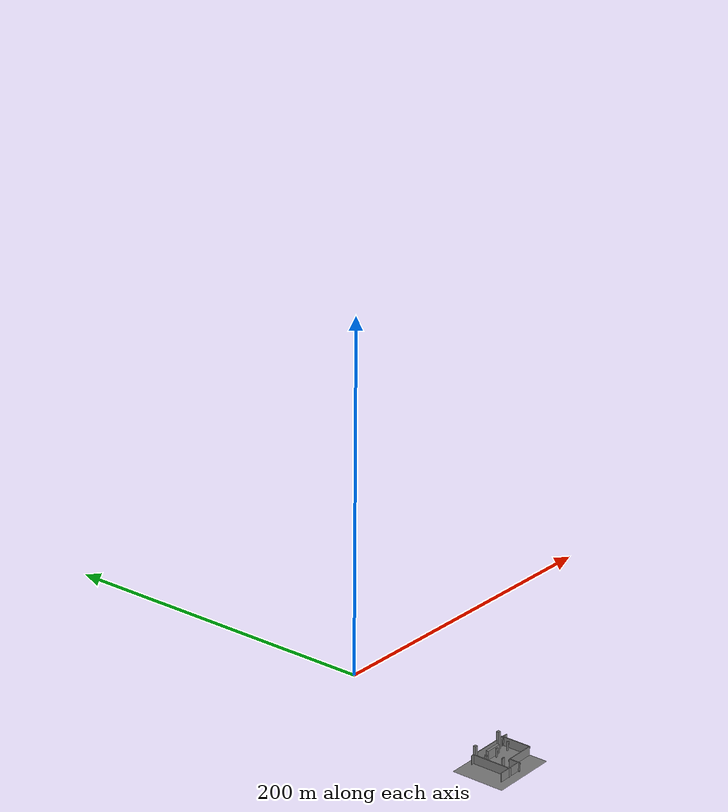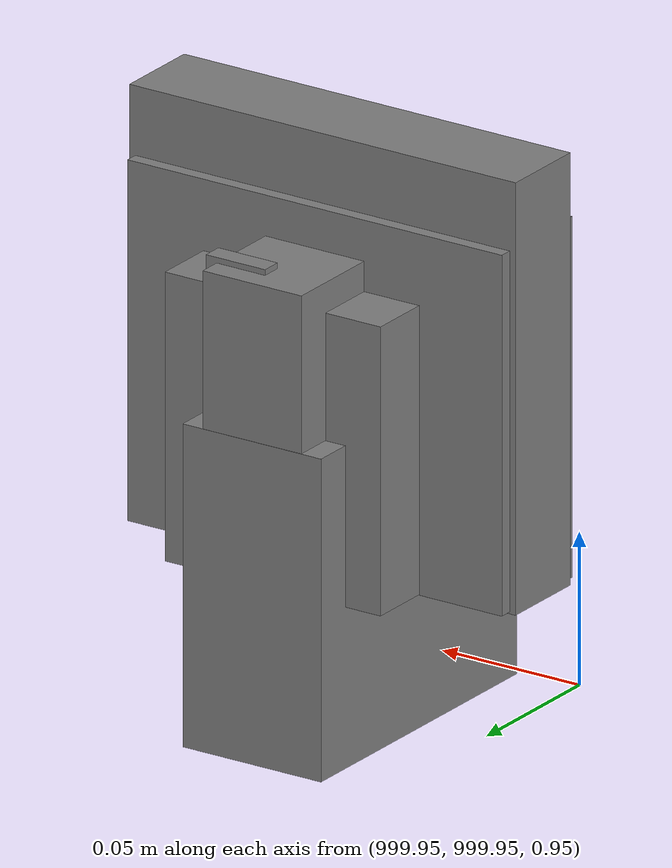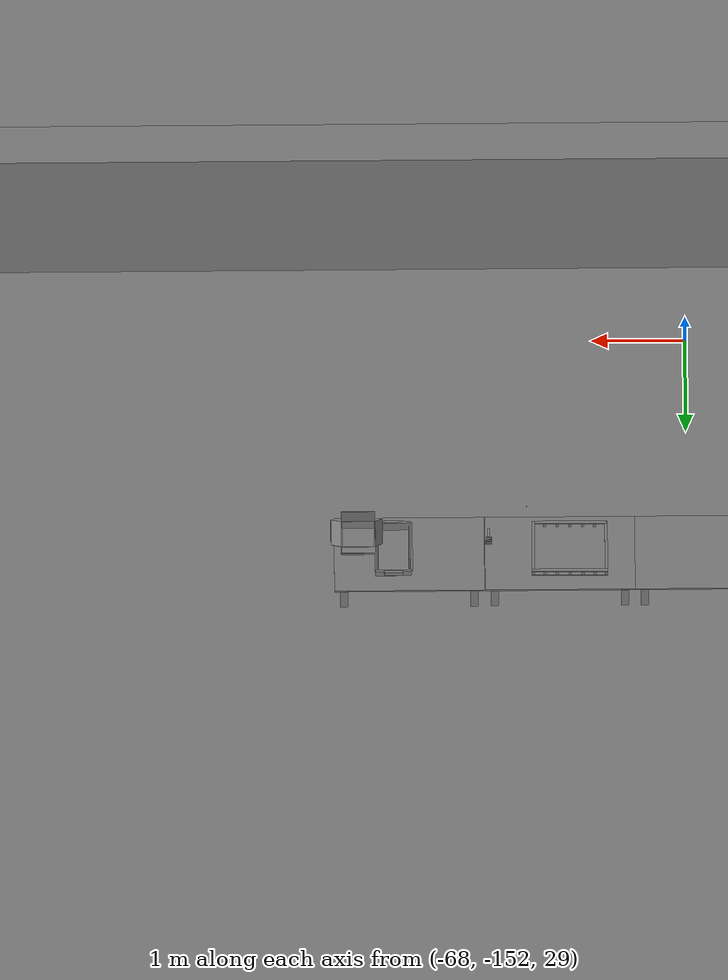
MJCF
<mujoco>
    <option gravity="0.000000000 0.000000000 -9.810000420" timestep="0.0049999999" integrator="implicitfast" density="1.225" viscosity="1.8000001e-05" noslip_iterations="10" iterations="100" sdf_iterations="50">
        <flag multiccd="disable"/>
    </option>
    <size memory="1000M"/>
    <compiler coordinate="local"/>
    <worldbody>
        <light cutoff="30" pos="0 1 1" dir="0 -1 -2"/>
        <light cutoff="30" pos="0 -1 1" dir="0 1 -2"/>
        <body pos="-64.866622925 -149.383972168 30.183746338" euler="89.999984741 89.999946594 0.000000000" name="openloong_gripper_2f85_fix_base_usda_bluebox_01">
            <geom contype="1" conaffinity="1" density="1000" type="box" material="" rgba="0.500000000 0.500000000 0.500000000 1.000000000" solimp="0.899999976 0.949999988 0.001000000" friction="1.000000000 0.005000000 0.000100000" solref="0.020000000 1.000000000" margin="0" condim="3" group="0" pos="0.276580811 0.187225342 0.000068665" quat="0.707106948 0.000077471 0.707106352 0.000077486" size="0.100000001 0.057999998 0.010000000" name="openloong_gripper_2f85_fix_base_usda_geom_90C03549_ACBE_4E7A_8ED3_CB8775F7B4FC"/>
            <geom contype="1" conaffinity="1" density="1000" type="box" material="" rgba="0.500000000 0.500000000 0.500000000 1.000000000" solimp="0.899999976 0.949999988 0.001000000" friction="1.000000000 0.005000000 0.000100000" solref="0.020000000 1.000000000" margin="0" condim="3" group="0" pos="0.000000000 0.002883911 0.000000000" quat="0.999999881 0.000000000 0.000000000 0.000000000" size="0.254000008 0.003000000 0.172000006" name="openloong_gripper_2f85_fix_base_usda_geom_5E4FAB1B_862D_442B_BFFB_4E2A0DE715CB"/>
            <geom contype="1" conaffinity="1" density="1000" type="box" material="" rgba="0.500000000 0.500000000 0.500000000 1.000000000" solimp="0.899999976 0.949999988 0.001000000" friction="1.000000000 0.005000000 0.000100000" solref="0.020000000 1.000000000" margin="0" condim="3" group="0" pos="0.000000000 0.124874115 0.173484802" quat="0.999796331 0.020176515 -0.000000015 0.000000030" size="0.259999990 0.119999997 0.007000000" name="openloong_gripper_2f85_fix_base_usda_geom_56008D38_B0F8_428F_A3EA_460C970AA9ED"/>
            <geom contype="1" conaffinity="1" density="1000" type="box" material="" rgba="0.500000000 0.500000000 0.500000000 1.000000000" solimp="0.899999976 0.949999988 0.001000000" friction="1.000000000 0.005000000 0.000100000" solref="0.020000000 1.000000000" margin="0" condim="3" group="0" pos="0.000000000 0.124874115 -0.173469543" quat="0.999796331 -0.020176545 -0.000000015 0.000000000" size="0.259999990 0.119999997 0.007000000" name="openloong_gripper_2f85_fix_base_usda_geom_D3FDBAE9_4292_4FCE_A431_775222F1C24D"/>
            <geom contype="1" conaffinity="1" density="1000" type="box" material="" rgba="0.500000000 0.500000000 0.500000000 1.000000000" solimp="0.899999976 0.949999988 0.001000000" friction="1.000000000 0.005000000 0.000100000" solref="0.020000000 1.000000000" margin="0" condim="3" group="0" pos="0.000000000 0.214008331 0.188980103" quat="0.999912977 0.013176724 0.000000015 0.000000000" size="0.259999990 0.029999999 0.012500000" name="openloong_gripper_2f85_fix_base_usda_geom_554BE7DF_52FA_432E_BB49_2E749DB490AB"/>
            <geom contype="1" conaffinity="1" density="1000" type="box" material="" rgba="0.500000000 0.500000000 0.500000000 1.000000000" solimp="0.899999976 0.949999988 0.001000000" friction="1.000000000 0.005000000 0.000100000" solref="0.020000000 1.000000000" margin="0" condim="3" group="0" pos="-0.258361816 0.125289917 0.001876831" quat="0.702796936 -0.020792112 0.710783124 0.020769298" size="0.189999998 0.119999997 0.009000000" name="openloong_gripper_2f85_fix_base_usda_geom_6D5F75F1_C37B_4C96_BD93_E894E1552048"/>
            <geom contype="1" conaffinity="1" density="1000" type="box" material="" rgba="0.500000000 0.500000000 0.500000000 1.000000000" solimp="0.899999976 0.949999988 0.001000000" friction="1.000000000 0.005000000 0.000100000" solref="0.020000000 1.000000000" margin="0" condim="3" group="0" pos="0.000000000 0.214008331 -0.188980103" quat="0.999912977 -0.013176769 0.000000030 0.000000015" size="0.259999990 0.029999999 0.012500000" name="openloong_gripper_2f85_fix_base_usda_geom_93516ABF_6277_458F_9114_BB4B75461C4A"/>
            <geom contype="1" conaffinity="1" density="1000" type="box" material="" rgba="0.500000000 0.500000000 0.500000000 1.000000000" solimp="0.899999976 0.949999988 0.001000000" friction="1.000000000 0.005000000 0.000100000" solref="0.020000000 1.000000000" margin="0" condim="3" group="0" pos="-0.276611328 0.187225342 0.000068665" quat="0.707106650 0.000077441 0.707106709 0.000077456" size="0.100000001 0.057999998 0.010000000" name="openloong_gripper_2f85_fix_base_usda_geom_1A4877AA_DAB0_4F4F_8679_CE206E9B72A1"/>
            <geom contype="1" conaffinity="1" density="1000" type="box" material="" rgba="0.500000000 0.500000000 0.500000000 1.000000000" solimp="0.899999976 0.949999988 0.001000000" friction="1.000000000 0.005000000 0.000100000" solref="0.020000000 1.000000000" margin="0" condim="3" group="0" pos="0.258331299 0.125289917 0.001876831" quat="0.702851415 0.018856421 0.710823774 -0.019329369" size="0.189999998 0.119999997 0.009000000" name="openloong_gripper_2f85_fix_base_usda_geom_F1651EFD_5990_44AD_92B1_F8BB1B803A01"/>
            <freejoint name="openloong_gripper_2f85_fix_base_usda_bluebox_01_joint"/>
            <site size="0.005000000 0.005000000 0.005000000" rgba="0.500000000 0.500000000 0.500000000 1.000000000" pos="0.000000000 0.000000000 0.000000000" quat="0.999961913 0.008726534 0.000000000 0.000000000" group="0" type="sphere" name="openloong_gripper_2f85_fix_base_usda_bluebox_01site"/>
        </body>
        <body pos="-64.496299744 -149.491867065 30.235729218" euler="0.000000000 0.000000000 89.999946594" name="openloong_gripper_2f85_fix_base_usda_cardboardbox_01">
            <geom contype="1" conaffinity="1" density="1000" type="box" material="" rgba="0.500000000 0.500000000 0.500000000 1.000000000" solimp="0.899999976 0.949999988 0.001000000" friction="1.000000000 0.005000000 0.000100000" solref="0.020000000 1.000000000" margin="0" condim="3" group="0" pos="-0.003166199 -0.004086494 0.005052090" quat="1.000000000 0.000000000 0.000000000 0.000000000" size="0.142499998 0.177500010 0.005000000" name="openloong_gripper_2f85_fix_base_usda_geom_C7F8F940_90A5_4AAC_9579_2D507F31047B"/>
            <geom contype="1" conaffinity="1" density="1000" type="box" material="" rgba="0.500000000 0.500000000 0.500000000 1.000000000" solimp="0.899999976 0.949999988 0.001000000" friction="1.000000000 0.005000000 0.000100000" solref="0.020000000 1.000000000" margin="0" condim="3" group="0" pos="-0.003166199 0.170316696 0.150570869" quat="1.000000000 0.000000000 0.000000000 0.000000000" size="0.142499998 0.005000000 0.149999991" name="openloong_gripper_2f85_fix_base_usda_geom_03A00BE5_E6C0_474C_938E_AC6244089464"/>
            <geom contype="1" conaffinity="1" density="1000" type="box" material="" rgba="0.500000000 0.500000000 0.500000000 1.000000000" solimp="0.899999976 0.949999988 0.001000000" friction="1.000000000 0.005000000 0.000100000" solref="0.020000000 1.000000000" margin="0" condim="3" group="0" pos="-0.147399902 -0.005307198 0.150570869" quat="1.000000000 0.000000000 0.000000000 0.000000000" size="0.005000000 0.177500010 0.149999991" name="openloong_gripper_2f85_fix_base_usda_geom_71859D71_CCAE_4B61_B85F_B486E615FCB3"/>
            <geom contype="1" conaffinity="1" density="1000" type="box" material="" rgba="0.500000000 0.500000000 0.500000000 1.000000000" solimp="0.899999976 0.949999988 0.001000000" friction="1.000000000 0.005000000 0.000100000" solref="0.020000000 1.000000000" margin="0" condim="3" group="0" pos="0.140275955 -0.005307198 0.150570869" quat="1.000000000 0.000000000 0.000000000 0.000000000" size="0.005000000 0.177500010 0.149999991" name="openloong_gripper_2f85_fix_base_usda_geom_35371C14_8502_49A0_9840_20093418A2A7"/>
            <geom contype="1" conaffinity="1" density="1000" type="box" material="" rgba="0.500000000 0.500000000 0.500000000 1.000000000" solimp="0.899999976 0.949999988 0.001000000" friction="1.000000000 0.005000000 0.000100000" solref="0.020000000 1.000000000" margin="0" condim="3" group="0" pos="-0.003166199 -0.181550980 0.150570869" quat="1.000000000 0.000000000 0.000000000 0.000000000" size="0.142499998 0.005000000 0.149999991" name="openloong_gripper_2f85_fix_base_usda_geom_B7FDDBCA_C88F_4DB7_BB0F_4C9844936292"/>
            <freejoint name="openloong_gripper_2f85_fix_base_usda_cardboardbox_01_joint"/>
            <site size="0.005000000 0.005000000 0.005000000" rgba="0.500000000 0.500000000 0.500000000 1.000000000" pos="0.000000000 0.000000000 0.000000000" quat="0.999961913 0.008726535 0.000000000 0.000000000" group="0" type="sphere" name="openloong_gripper_2f85_fix_base_usda_site_9681A805_4EAA_4A15_B6D5_C5D5CAC564DD"/>
            <body pos="0.139160156 -0.004048347 0.301930904" euler="-179.999954224 49.383502960 179.999954224" name="openloong_gripper_2f85_fix_base_usda_A1_006">
                <geom contype="1" conaffinity="1" density="1000" type="box" material="" rgba="0.500000000 0.500000000 0.500000000 1.000000000" solimp="0.899999976 0.949999988 0.001000000" friction="1.000000000 0.005000000 0.000100000" solref="0.020000000 1.000000000" margin="0" condim="3" group="0" pos="-0.071587563 0.000009537 0.001745224" quat="0.999999881 0.000000000 0.000000000 0.000000000" size="0.071249999 0.179999992 0.002500000" name="openloong_gripper_2f85_fix_base_usda_geom_6C2849DC_3B6D_4184_9AB2_BB95C103C978"/>
                <joint armature="0" stiffness="0.07" damping="0.0099999998" axis="0.000000 1.000000 0.000000" type="hinge" name="openloong_gripper_2f85_fix_base_usda_A1_006"/>
            </body>
            <body pos="-0.145902634 -0.004086494 0.301938057" euler="-180.000000000 -60.000011444 -180.000000000" name="openloong_gripper_2f85_fix_base_usda_A2_006">
                <geom contype="1" conaffinity="1" density="1000" type="box" material="" rgba="0.500000000 0.500000000 0.500000000 1.000000000" solimp="0.899999976 0.949999988 0.001000000" friction="1.000000000 0.005000000 0.000100000" solref="0.020000000 1.000000000" margin="0" condim="3" group="0" pos="0.071268082 0.000009537 0.002717972" quat="0.000002921 0.000000000 -0.000000030 0.999999881" size="0.071249999 0.179999992 0.002500000" name="openloong_gripper_2f85_fix_base_usda_geom_895BD3C5_480F_4FCE_AB83_3DA55C9C040D"/>
                <joint armature="0" stiffness="0.07" damping="0.0099999998" axis="0.000000 1.000000 0.000000" type="hinge" name="openloong_gripper_2f85_fix_base_usda_A2_006"/>
            </body>
            <body pos="-0.003385544 0.175991058 0.301930904" euler="-125.858116150 -0.000004561 0.000002331" name="openloong_gripper_2f85_fix_base_usda_B2_006">
                <geom contype="1" conaffinity="1" density="1000" type="box" material="" rgba="0.500000000 0.500000000 0.500000000 1.000000000" solimp="0.899999976 0.949999988 0.001000000" friction="1.000000000 0.005000000 0.000100000" solref="0.020000000 1.000000000" margin="0" condim="3" group="0" pos="0.000009537 -0.070939064 -0.002470016" quat="0.999614120 0.027776197 -0.000000015 0.000000030" size="0.137500003 0.064999998 0.005000000" name="openloong_gripper_2f85_fix_base_usda_geom_82263F13_C538_4326_8CF2_F60F6B514A45"/>
                <joint armature="0" stiffness="0.07" damping="0.0099999998" axis="1.000000 0.000000 0.000000" type="hinge" name="openloong_gripper_2f85_fix_base_usda_B2_006"/>
            </body>
            <body pos="-0.003385544 -0.184140205 0.301938057" euler="147.805557251 0.000000000 0.000000000" name="openloong_gripper_2f85_fix_base_usda_B1_006">
                <geom contype="1" conaffinity="1" density="1000" type="box" material="" rgba="0.500000000 0.500000000 0.500000000 1.000000000" solimp="0.899999976 0.949999988 0.001000000" friction="1.000000000 0.005000000 0.000100000" solref="0.020000000 1.000000000" margin="0" condim="3" group="0" pos="-0.000028610 0.070202351 -0.002703667" quat="0.999614179 -0.027776167 0.000000000 0.000000000" size="0.137500003 0.064999998 0.005000000" name="openloong_gripper_2f85_fix_base_usda_geom_4097EC52_EFE8_4E5D_80C2_D3814E55F544"/>
                <joint armature="0" stiffness="0.07" damping="0.0099999998" axis="1.000000 0.000000 0.000000" type="hinge" name="openloong_gripper_2f85_fix_base_usda_B1_006"/>
            </body>
        </body>
        <body pos="-65.882858276 -149.481979370 30.229999542" euler="-64.487716675 0.000000000 0.000000000" name="openloong_gripper_2f85_fix_base_usda_Barcode">
            <geom contype="1" conaffinity="1" density="1000" type="box" material="" rgba="0.500000000 0.500000000 0.500000000 1.000000000" solimp="0.899999976 0.949999988 0.001000000" friction="1.000000000 0.005000000 0.000100000" solref="0.020000000 1.000000000" margin="0" condim="3" group="0" pos="0.000000000 0.013038635 0.001419067" quat="0.000000000 0.000000000 0.000000000 1.000000119" size="0.034000002 0.010000000 0.017999999" name="openloong_gripper_2f85_fix_base_usda_geom_7A07FA69_F2C6_4BF2_8FB3_54444837E682"/>
            <geom contype="1" conaffinity="1" density="1000" type="box" material="" rgba="0.500000000 0.500000000 0.500000000 1.000000000" solimp="0.899999976 0.949999988 0.001000000" friction="1.000000000 0.005000000 0.000100000" solref="0.020000000 1.000000000" margin="0" condim="3" group="0" pos="0.000000000 -0.035301208 -0.007095337" quat="0.000000000 0.000000000 -0.043619365 0.999048233" size="0.028999999 0.010000000 0.020000000" name="openloong_gripper_2f85_fix_base_usda_geom_A8A13FED_06F8_4971_B5DD_4324D0EE277F"/>
            <geom contype="1" conaffinity="1" density="1000" type="box" material="" rgba="0.500000000 0.500000000 0.500000000 1.000000000" solimp="0.899999976 0.949999988 0.001000000" friction="1.000000000 0.005000000 0.000100000" solref="0.020000000 1.000000000" margin="0" condim="3" group="0" pos="0.000000000 -0.043411255 -0.011749268" quat="0.922262907 0.386563420 0.000000000 0.000000000" size="0.026000001 0.010000000 0.020000000" name="openloong_gripper_2f85_fix_base_usda_geom_CBC210EF_EBF0_4575_9F4A_037BFBE1BFD6"/>
            <geom contype="1" conaffinity="1" density="1000" type="box" material="" rgba="0.500000000 0.500000000 0.500000000 1.000000000" solimp="0.899999976 0.949999988 0.001000000" friction="1.000000000 0.005000000 0.000100000" solref="0.020000000 1.000000000" margin="0" condim="3" group="0" pos="0.000000000 -0.016967773 -0.031860352" quat="0.000000000 0.000000000 0.000000000 1.000000119" size="0.008000000 0.010000000 0.013000000" name="openloong_gripper_2f85_fix_base_usda_geom_2EA480BD_DBE4_4A2A_8EEE_FCE8E2627670"/>
            <geom contype="1" conaffinity="1" density="1000" type="box" material="" rgba="0.500000000 0.500000000 0.500000000 1.000000000" solimp="0.899999976 0.949999988 0.001000000" friction="1.000000000 0.005000000 0.000100000" solref="0.020000000 1.000000000" margin="0" condim="3" group="0" pos="0.000000000 -0.001869202 0.000312805" quat="0.953716993 0.300705761 0.000000000 0.000000000" size="0.032000002 0.010000000 0.018999999" name="openloong_gripper_2f85_fix_base_usda_geom_3D5186E0_ADCC_468B_BAEF_044D9B11BB27"/>
            <geom contype="1" conaffinity="1" density="1000" type="box" material="" rgba="0.500000000 0.500000000 0.500000000 1.000000000" solimp="0.899999976 0.949999988 0.001000000" friction="1.000000000 0.005000000 0.000100000" solref="0.020000000 1.000000000" margin="0" condim="3" group="0" pos="0.000000000 -0.019531250 -0.003173828" quat="0.953716993 0.300705761 0.000000000 0.000000000" size="0.030999999 0.010000000 0.020000000" name="openloong_gripper_2f85_fix_base_usda_geom_4CDB6511_040A_4FD7_9A34_EB6B7203A670"/>
            <geom contype="1" conaffinity="1" density="1000" type="box" material="" rgba="0.500000000 0.500000000 0.500000000 1.000000000" solimp="0.899999976 0.949999988 0.001000000" friction="1.000000000 0.005000000 0.000100000" solref="0.020000000 1.000000000" margin="0" condim="3" group="0" pos="0.000000000 -0.035301208 -0.007095337" quat="0.953716993 0.300705761 0.000000000 0.000000000" size="0.028999999 0.010000000 0.020000000" name="openloong_gripper_2f85_fix_base_usda_geom_2BFCA481_7FC5_400C_BB7C_BF931E1B6497"/>
            <geom contype="1" conaffinity="1" density="1000" type="box" material="" rgba="0.500000000 0.500000000 0.500000000 1.000000000" solimp="0.899999976 0.949999988 0.001000000" friction="1.000000000 0.005000000 0.000100000" solref="0.020000000 1.000000000" margin="0" condim="3" group="0" pos="0.000000000 -0.042617798 -0.071121216" quat="0.000000000 0.000000000 0.000000000 1.000000119" size="0.013000000 0.021000000 0.059999999" name="openloong_gripper_2f85_fix_base_usda_geom_BFF53183_301A_4DFE_A5BC_7A4C4A006B2C"/>
            <freejoint name="openloong_gripper_2f85_fix_base_usda_Barcode_joint"/>
            <site size="0.005000000 0.005000000 0.005000000" rgba="0.500000000 0.500000000 0.500000000 1.000000000" pos="0.000000000 0.000000000 0.000000000" quat="1.000000000 0.000000000 0.000000000 0.000000000" group="0" type="sphere" name="openloong_gripper_2f85_fix_base_usda_Barcode_site"/>
        </body>
        <body pos="-66.745018005 -149.392349243 30.184000015" euler="0.000000000 0.000000000 89.999946594" name="[22329964453603]_Basket_01">
            <geom contype="1" conaffinity="1" density="1000" type="box" material="" rgba="0.500000000 0.500000000 0.500000000 1.000000000" solimp="0.899999976 0.949999988 0.001000000" friction="1.000000000 0.005000000 0.000100000" solref="0.020000000 1.000000000" margin="0" condim="3" group="0" pos="-0.052425385 0.389207840 0.089787483" quat="0.707107008 0.000000000 0.000000000 0.707106411" size="0.014249999 0.014249999 0.059999999" name="[22329964453603]_geom_CFDD9B23_7F47_484B_A443_742C00605F80"/>
            <geom contype="1" conaffinity="1" density="1000" type="box" material="" rgba="0.500000000 0.500000000 0.500000000 1.000000000" solimp="0.899999976 0.949999988 0.001000000" friction="1.000000000 0.005000000 0.000100000" solref="0.020000000 1.000000000" margin="0" condim="3" group="0" pos="0.264015198 -0.133043289 0.089787483" quat="0.707107008 0.000000000 0.000000000 0.707106411" size="0.014249999 0.014249999 0.059999999" name="[22329964453603]_geom_A5B42A19_D43D_44F1_BF2B_771C3A0EBCAD"/>
            <geom contype="1" conaffinity="1" density="1000" type="box" material="" rgba="0.500000000 0.500000000 0.500000000 1.000000000" solimp="0.899999976 0.949999988 0.001000000" friction="1.000000000 0.005000000 0.000100000" solref="0.020000000 1.000000000" margin="0" condim="3" group="0" pos="-0.264015198 -0.265548706 0.089793205" quat="0.707107008 0.000000000 0.000000000 0.707106411" size="0.014249999 0.014249999 0.059999999" name="[22329964453603]_geom_CB3D0F6B_4500_4B2A_A40D_DA7CB747AE6C"/>
            <geom contype="1" conaffinity="1" density="1000" type="box" material="" rgba="0.500000000 0.500000000 0.500000000 1.000000000" solimp="0.899999976 0.949999988 0.001000000" friction="1.000000000 0.005000000 0.000100000" solref="0.020000000 1.000000000" margin="0" condim="3" group="0" pos="-0.160263062 -0.389322281 0.089793205" quat="0.707107008 0.000000000 0.000000000 0.707106411" size="0.014249999 0.014249999 0.059999999" name="[22329964453603]_geom_B732AA2A_0C01_485C_AF73_89ACD0620AA0"/>
            <geom contype="1" conaffinity="1" density="1000" type="box" material="" rgba="0.500000000 0.500000000 0.500000000 1.000000000" solimp="0.899999976 0.949999988 0.001000000" friction="1.000000000 0.005000000 0.000100000" solref="0.020000000 1.000000000" margin="0" condim="3" group="0" pos="0.162265778 -0.389322281 0.089787483" quat="0.707107008 0.000000000 0.000000000 0.707106411" size="0.014249999 0.014249999 0.059999999" name="[22329964453603]_geom_4FC60FAE_E74C_42EF_82B8_DF7D07AD51D3"/>
            <geom contype="1" conaffinity="1" density="1000" type="box" material="" rgba="0.500000000 0.500000000 0.500000000 1.000000000" solimp="0.899999976 0.949999988 0.001000000" friction="1.000000000 0.005000000 0.000100000" solref="0.020000000 1.000000000" margin="0" condim="3" group="0" pos="0.264015198 0.389207840 0.089787483" quat="0.707107008 0.000000000 0.000000000 0.707106411" size="0.014249999 0.014249999 0.059999999" name="[22329964453603]_geom_70CC4D38_30C2_46AD_ACDB_51BBB50F6697"/>
            <geom contype="1" conaffinity="1" density="1000" type="box" material="" rgba="0.500000000 0.500000000 0.500000000 1.000000000" solimp="0.899999976 0.949999988 0.001000000" friction="1.000000000 0.005000000 0.000100000" solref="0.020000000 1.000000000" margin="0" condim="3" group="0" pos="-0.264015198 -0.133043289 0.089793205" quat="0.707107008 0.000000000 0.000000000 0.707106411" size="0.014249999 0.014249999 0.059999999" name="[22329964453603]_geom_EF63B6D2_003F_4B06_975F_1296BB437E35"/>
            <geom contype="1" conaffinity="1" density="1000" type="box" material="" rgba="0.500000000 0.500000000 0.500000000 1.000000000" solimp="0.899999976 0.949999988 0.001000000" friction="1.000000000 0.005000000 0.000100000" solref="0.020000000 1.000000000" margin="0" condim="3" group="0" pos="-0.264026642 0.269256592 0.089793205" quat="0.707107008 0.000000000 0.000000000 0.707106411" size="0.014249999 0.014249999 0.059999999" name="[22329964453603]_geom_5BF69573_4A54_4934_A0E8_CED2D98BDC3B"/>
            <geom contype="1" conaffinity="1" density="1000" type="box" material="" rgba="0.500000000 0.500000000 0.500000000 1.000000000" solimp="0.899999976 0.949999988 0.001000000" friction="1.000000000 0.005000000 0.000100000" solref="0.020000000 1.000000000" margin="0" condim="3" group="0" pos="0.054462433 0.389207840 0.089787483" quat="0.707107008 0.000000000 0.000000000 0.707106411" size="0.014249999 0.014249999 0.059999999" name="[22329964453603]_geom_C9C4D28B_F45C_4C8D_B321_0B82F1A87C45"/>
            <geom contype="1" conaffinity="1" density="1000" type="box" material="" rgba="0.500000000 0.500000000 0.500000000 1.000000000" solimp="0.899999976 0.949999988 0.001000000" friction="1.000000000 0.005000000 0.000100000" solref="0.020000000 1.000000000" margin="0" condim="3" group="0" pos="0.054462433 -0.389322281 0.089787483" quat="0.707107008 0.000000000 0.000000000 0.707106411" size="0.014249999 0.014249999 0.059999999" name="[22329964453603]_geom_0E7129B1_11C2_4B34_A982_8EC6B3061620"/>
            <geom contype="1" conaffinity="1" density="1000" type="box" material="" rgba="0.500000000 0.500000000 0.500000000 1.000000000" solimp="0.899999976 0.949999988 0.001000000" friction="1.000000000 0.005000000 0.000100000" solref="0.020000000 1.000000000" margin="0" condim="3" group="0" pos="0.264015198 0.269256592 0.089793205" quat="0.707107008 0.000000000 0.000000000 0.707106411" size="0.014249999 0.014249999 0.059999999" name="[22329964453603]_geom_608AF851_440E_4E98_A45B_559F457C8C7D"/>
            <geom contype="1" conaffinity="1" density="1000" type="box" material="" rgba="0.500000000 0.500000000 0.500000000 1.000000000" solimp="0.899999976 0.949999988 0.001000000" friction="1.000000000 0.005000000 0.000100000" solref="0.020000000 1.000000000" margin="0" condim="3" group="0" pos="0.264015198 -0.389322281 0.089787483" quat="0.707107008 0.000000000 0.000000000 0.707106411" size="0.014249999 0.014249999 0.059999999" name="[22329964453603]_geom_FF82F775_F751_4963_839C_00646C9A2E69"/>
            <geom contype="1" conaffinity="1" density="1000" type="box" material="" rgba="0.500000000 0.500000000 0.500000000 1.000000000" solimp="0.899999976 0.949999988 0.001000000" friction="1.000000000 0.005000000 0.000100000" solref="0.020000000 1.000000000" margin="0" condim="3" group="0" pos="0.000000000 0.000000000 0.015998840" quat="0.707107008 0.000000000 0.000000000 0.707106411" size="0.403499991 0.279000014 0.015750000" name="[22329964453603]_geom_25B87FD2_8EBB_4624_BDEB_DF88F0B133DC"/>
            <geom contype="1" conaffinity="1" density="1000" type="box" material="" rgba="0.500000000 0.500000000 0.500000000 1.000000000" solimp="0.899999976 0.949999988 0.001000000" friction="1.000000000 0.005000000 0.000100000" solref="0.020000000 1.000000000" margin="0" condim="3" group="0" pos="0.000000000 -0.389476776 0.163619041" quat="0.707107008 0.000000000 0.000000000 0.707106411" size="0.015000000 0.277500004 0.015750000" name="[22329964453603]_geom_7B093280_23AA_4078_8FB2_392ED3B93A15"/>
            <geom contype="1" conaffinity="1" density="1000" type="box" material="" rgba="0.500000000 0.500000000 0.500000000 1.000000000" solimp="0.899999976 0.949999988 0.001000000" friction="1.000000000 0.005000000 0.000100000" solref="0.020000000 1.000000000" margin="0" condim="3" group="0" pos="0.162265778 0.389207840 0.089787483" quat="0.707107008 0.000000000 0.000000000 0.707106411" size="0.014249999 0.014249999 0.059999999" name="[22329964453603]_geom_162CE7FE_F5F0_4383_88FD_1C249BAD5C44"/>
            <geom contype="1" conaffinity="1" density="1000" type="box" material="" rgba="0.500000000 0.500000000 0.500000000 1.000000000" solimp="0.899999976 0.949999988 0.001000000" friction="1.000000000 0.005000000 0.000100000" solref="0.020000000 1.000000000" margin="0" condim="3" group="0" pos="0.000000000 0.389471054 0.163619041" quat="0.707107008 0.000000000 0.000000000 0.707106411" size="0.015000000 0.277500004 0.015750000" name="[22329964453603]_geom_44D6BD33_E7F0_400D_9D6B_DCEBE401A357"/>
            <geom contype="1" conaffinity="1" density="1000" type="box" material="" rgba="0.500000000 0.500000000 0.500000000 1.000000000" solimp="0.899999976 0.949999988 0.001000000" friction="1.000000000 0.005000000 0.000100000" solref="0.020000000 1.000000000" margin="0" condim="3" group="0" pos="-0.263511658 0.000000000 0.163619041" quat="0.707107008 0.000000000 0.000000000 0.707106411" size="0.403499991 0.015000000 0.015750000" name="[22329964453603]_geom_6BB5C99C_6EF1_4C9C_A5B5_431B7745A3E6"/>
            <geom contype="1" conaffinity="1" density="1000" type="box" material="" rgba="0.500000000 0.500000000 0.500000000 1.000000000" solimp="0.899999976 0.949999988 0.001000000" friction="1.000000000 0.005000000 0.000100000" solref="0.020000000 1.000000000" margin="0" condim="3" group="0" pos="-0.264015198 0.141334534 0.089793205" quat="0.707107008 0.000000000 0.000000000 0.707106411" size="0.014249999 0.014249999 0.059999999" name="[22329964453603]_geom_63593393_F522_4649_9032_2C8C95DB5740"/>
            <geom contype="1" conaffinity="1" density="1000" type="box" material="" rgba="0.500000000 0.500000000 0.500000000 1.000000000" solimp="0.899999976 0.949999988 0.001000000" friction="1.000000000 0.005000000 0.000100000" solref="0.020000000 1.000000000" margin="0" condim="3" group="0" pos="0.264015198 -0.265548706 0.089787483" quat="0.707107008 0.000000000 0.000000000 0.707106411" size="0.014249999 0.014249999 0.059999999" name="[22329964453603]_geom_1BE6E06C_FEDA_4CAA_A24E_181A897DEF86"/>
            <geom contype="1" conaffinity="1" density="1000" type="box" material="" rgba="0.500000000 0.500000000 0.500000000 1.000000000" solimp="0.899999976 0.949999988 0.001000000" friction="1.000000000 0.005000000 0.000100000" solref="0.020000000 1.000000000" margin="0" condim="3" group="0" pos="-0.160263062 0.389207840 0.089787483" quat="0.707107008 0.000000000 0.000000000 0.707106411" size="0.014249999 0.014249999 0.059999999" name="[22329964453603]_geom_571B3F36_5BA1_4BC7_ABEA_A475C763EA6E"/>
            <geom contype="1" conaffinity="1" density="1000" type="box" material="" rgba="0.500000000 0.500000000 0.500000000 1.000000000" solimp="0.899999976 0.949999988 0.001000000" friction="1.000000000 0.005000000 0.000100000" solref="0.020000000 1.000000000" margin="0" condim="3" group="0" pos="-0.052425385 -0.389322281 0.089787483" quat="0.707107008 0.000000000 0.000000000 0.707106411" size="0.014249999 0.014249999 0.059999999" name="[22329964453603]_geom_1AE65B54_F168_42FE_883C_656DA12485C8"/>
            <geom contype="1" conaffinity="1" density="1000" type="box" material="" rgba="0.500000000 0.500000000 0.500000000 1.000000000" solimp="0.899999976 0.949999988 0.001000000" friction="1.000000000 0.005000000 0.000100000" solref="0.020000000 1.000000000" margin="0" condim="3" group="0" pos="-0.264026642 -0.389322281 0.089793205" quat="0.707107008 0.000000000 0.000000000 0.707106411" size="0.014249999 0.014249999 0.059999999" name="[22329964453603]_geom_3386055F_37F5_41D8_83B0_563E9D5AF4FF"/>
            <geom contype="1" conaffinity="1" density="1000" type="box" material="" rgba="0.500000000 0.500000000 0.500000000 1.000000000" solimp="0.899999976 0.949999988 0.001000000" friction="1.000000000 0.005000000 0.000100000" solref="0.020000000 1.000000000" margin="0" condim="3" group="0" pos="0.264015198 0.141334534 0.089787483" quat="0.707107008 0.000000000 0.000000000 0.707106411" size="0.014249999 0.014249999 0.059999999" name="[22329964453603]_geom_1B91B397_7080_4F8F_9AC5_55E8820BF5AF"/>
            <geom contype="1" conaffinity="1" density="1000" type="box" material="" rgba="0.500000000 0.500000000 0.500000000 1.000000000" solimp="0.899999976 0.949999988 0.001000000" friction="1.000000000 0.005000000 0.000100000" solref="0.020000000 1.000000000" margin="0" condim="3" group="0" pos="-0.264015198 0.389207840 0.089793205" quat="0.707107008 0.000000000 0.000000000 0.707106411" size="0.014249999 0.014249999 0.059999999" name="[22329964453603]_geom_72607795_4FB4_4020_9800_BA7C7236A51D"/>
            <geom contype="1" conaffinity="1" density="1000" type="box" material="" rgba="0.500000000 0.500000000 0.500000000 1.000000000" solimp="0.899999976 0.949999988 0.001000000" friction="1.000000000 0.005000000 0.000100000" solref="0.020000000 1.000000000" margin="0" condim="3" group="0" pos="0.264015198 0.004480362 0.089787483" quat="0.707107008 0.000000000 0.000000000 0.707106411" size="0.014249999 0.014249999 0.059999999" name="[22329964453603]_geom_A7E12C28_1E2D_45DE_ACEC_34E3EFAE9EEA"/>
            <geom contype="1" conaffinity="1" density="1000" type="box" material="" rgba="0.500000000 0.500000000 0.500000000 1.000000000" solimp="0.899999976 0.949999988 0.001000000" friction="1.000000000 0.005000000 0.000100000" solref="0.020000000 1.000000000" margin="0" condim="3" group="0" pos="0.263694763 -0.000011444 0.163619041" quat="0.707107008 0.000000000 0.000000000 0.707106411" size="0.403499991 0.015000000 0.015750000" name="[22329964453603]_geom_31B745EE_D1C4_493F_A580_950D5E0DBB0F"/>
            <geom contype="1" conaffinity="1" density="1000" type="box" material="" rgba="0.500000000 0.500000000 0.500000000 1.000000000" solimp="0.899999976 0.949999988 0.001000000" friction="1.000000000 0.005000000 0.000100000" solref="0.020000000 1.000000000" margin="0" condim="3" group="0" pos="-0.264015198 0.004480362 0.089793205" quat="0.707107008 0.000000000 0.000000000 0.707106411" size="0.014249999 0.014249999 0.059999999" name="[22329964453603]_geom_22CB7040_E64A_48F8_AAC9_207FD464AC29"/>
            <freejoint name="[22329964453603]_joint_610E189D_D92D_4B14_A65E_B53130A392AC"/>
        </body>
        <body pos="0.000000000 0.000000000 0.000000000" euler="0.000000000 0.000000000 0.000000000" name="Static Objects_Static Objects">
            <geom contype="1" conaffinity="1" density="1000" type="box" material="" rgba="0.500000000 0.500000000 0.500000000 1.000000000" solimp="0.899999976 0.949999988 0.001000000" friction="1.000000000 0.005000000 0.000100000" solref="0.020000000 1.000000000" margin="0" condim="3" group="0" pos="-67.544113159 -149.365814209 29.727830887" quat="0.500000417 0.499999970 0.499999553 0.499999970" size="0.381000012 0.319999993 0.041000001" name="Static Objects_geom_52C3A9BE_34F5_4065_B4FD_1BBB58E99510"/>
            <geom contype="1" conaffinity="1" density="1000" type="box" material="" rgba="0.500000000 0.500000000 0.500000000 1.000000000" solimp="0.899999976 0.949999988 0.001000000" friction="1.000000000 0.005000000 0.000100000" solref="0.020000000 1.000000000" margin="0" condim="3" group="0" pos="-68.239501953 -149.365814209 30.086868286" quat="0.500000417 0.499999970 0.499999553 0.499999970" size="0.370999992 0.039500002 0.745000005" name="Static Objects_geom_2AD96E3F_CFE3_41F6_ABBF_83C4A221A490"/>
            <geom contype="1" conaffinity="1" density="1000" type="box" material="" rgba="0.500000000 0.500000000 0.500000000 1.000000000" solimp="0.899999976 0.949999988 0.001000000" friction="1.000000000 0.005000000 0.000100000" solref="0.020000000 1.000000000" margin="0" condim="3" group="0" pos="-68.239501953 -149.365814209 30.147235870" quat="0.500000417 0.499999970 0.499999553 0.499999970" size="0.400000006 0.022000000 0.800000012" name="Static Objects_geom_3D0B01CE_18B1_484D_B418_5298C7CCE558"/>
            <geom contype="1" conaffinity="1" density="1000" type="box" material="" rgba="0.500000000 0.500000000 0.500000000 1.000000000" solimp="0.899999976 0.949999988 0.001000000" friction="1.000000000 0.005000000 0.000100000" solref="0.020000000 1.000000000" margin="0" condim="3" group="0" pos="-68.934890747 -149.365814209 29.727830887" quat="0.500000417 0.499999970 0.499999553 0.499999970" size="0.381000012 0.319999993 0.041000001" name="Static Objects_geom_03B56140_95A0_40CA_AEBF_DA191CA99ACB"/>
            <geom contype="1" conaffinity="1" density="1000" type="box" material="" rgba="0.500000000 0.500000000 0.500000000 1.000000000" solimp="0.899999976 0.949999988 0.001000000" friction="1.000000000 0.005000000 0.000100000" solref="0.020000000 1.000000000" margin="0" condim="3" group="0" pos="-68.239501953 -149.365814209 29.561563492" quat="0.500000417 0.499999970 0.499999553 0.499999970" size="0.020000000 0.022000000 0.660000026" name="Static Objects_geom_F4D855D5_FB88_47AB_8459_AD36D0B95E27"/>
            <geom contype="1" conaffinity="1" density="1000" type="box" material="" rgba="0.500000000 0.500000000 0.500000000 1.000000000" solimp="0.899999976 0.949999988 0.001000000" friction="1.000000000 0.005000000 0.000100000" solref="0.020000000 1.000000000" margin="0" condim="3" group="0" pos="-65.945671082 -149.365814209 29.727830887" quat="0.500000417 0.499999970 0.499999553 0.499999970" size="0.381000012 0.319999993 0.041000001" name="Static Objects_geom_33D2BBFF_F8AD_4314_B978_CC4F16F13407"/>
            <geom contype="1" conaffinity="1" density="1000" type="box" material="" rgba="0.500000000 0.500000000 0.500000000 1.000000000" solimp="0.899999976 0.949999988 0.001000000" friction="1.000000000 0.005000000 0.000100000" solref="0.020000000 1.000000000" margin="0" condim="3" group="0" pos="-66.641059875 -149.365814209 30.086868286" quat="0.500000417 0.499999970 0.499999553 0.499999970" size="0.370999992 0.039500002 0.745000005" name="Static Objects_geom_02720701_7227_44B2_B7BD_940CAF954A80"/>
            <geom contype="1" conaffinity="1" density="1000" type="box" material="" rgba="0.500000000 0.500000000 0.500000000 1.000000000" solimp="0.899999976 0.949999988 0.001000000" friction="1.000000000 0.005000000 0.000100000" solref="0.020000000 1.000000000" margin="0" condim="3" group="0" pos="-66.641059875 -149.365814209 30.147235870" quat="0.500000417 0.499999970 0.499999553 0.499999970" size="0.400000006 0.022000000 0.800000012" name="Static Objects_geom_F932F936_ACCD_4FEC_AFFD_29ABB6CA18F3"/>
            <geom contype="1" conaffinity="1" density="1000" type="box" material="" rgba="0.500000000 0.500000000 0.500000000 1.000000000" solimp="0.899999976 0.949999988 0.001000000" friction="1.000000000 0.005000000 0.000100000" solref="0.020000000 1.000000000" margin="0" condim="3" group="0" pos="-67.336448669 -149.365814209 29.727830887" quat="0.500000417 0.499999970 0.499999553 0.499999970" size="0.381000012 0.319999993 0.041000001" name="Static Objects_geom_C132FDC4_AD30_4936_BED4_9C10D1D4C176"/>
            <geom contype="1" conaffinity="1" density="1000" type="box" material="" rgba="0.500000000 0.500000000 0.500000000 1.000000000" solimp="0.899999976 0.949999988 0.001000000" friction="1.000000000 0.005000000 0.000100000" solref="0.020000000 1.000000000" margin="0" condim="3" group="0" pos="-66.641059875 -149.365814209 29.561563492" quat="0.500000417 0.499999970 0.499999553 0.499999970" size="0.020000000 0.022000000 0.660000026" name="Static Objects_geom_37CB0DEE_CCA5_4160_A9C0_E1E42909800A"/>
            <geom contype="1" conaffinity="1" density="1000" type="box" material="" rgba="0.500000000 0.500000000 0.500000000 1.000000000" solimp="0.899999976 0.949999988 0.001000000" friction="1.000000000 0.005000000 0.000100000" solref="0.020000000 1.000000000" margin="0" condim="3" group="0" pos="-64.338577271 -149.365814209 29.727830887" quat="0.500000417 0.499999970 0.499999553 0.499999970" size="0.381000012 0.319999993 0.041000001" name="Static Objects_geom_DFF8901A_458F_4DAE_8201_5DE6D55FDE42"/>
            <geom contype="1" conaffinity="1" density="1000" type="box" material="" rgba="0.500000000 0.500000000 0.500000000 1.000000000" solimp="0.899999976 0.949999988 0.001000000" friction="1.000000000 0.005000000 0.000100000" solref="0.020000000 1.000000000" margin="0" condim="3" group="0" pos="-65.033966064 -149.365814209 30.086868286" quat="0.500000417 0.499999970 0.499999553 0.499999970" size="0.370999992 0.039500002 0.745000005" name="Static Objects_geom_EEE4C481_605F_4F32_8AA4_EA51884F9DC8"/>
            <geom contype="1" conaffinity="1" density="1000" type="box" material="" rgba="0.500000000 0.500000000 0.500000000 1.000000000" solimp="0.899999976 0.949999988 0.001000000" friction="1.000000000 0.005000000 0.000100000" solref="0.020000000 1.000000000" margin="0" condim="3" group="0" pos="-65.033966064 -149.365814209 30.147235870" quat="0.500000417 0.499999970 0.499999553 0.499999970" size="0.400000006 0.022000000 0.800000012" name="Static Objects_geom_E01A10DF_46F9_43DE_B0F5_C9143FEE243E"/>
            <geom contype="1" conaffinity="1" density="1000" type="box" material="" rgba="0.500000000 0.500000000 0.500000000 1.000000000" solimp="0.899999976 0.949999988 0.001000000" friction="1.000000000 0.005000000 0.000100000" solref="0.020000000 1.000000000" margin="0" condim="3" group="0" pos="-65.729354858 -149.365814209 29.727830887" quat="0.500000417 0.499999970 0.499999553 0.499999970" size="0.381000012 0.319999993 0.041000001" name="Static Objects_geom_84BEC74C_D7ED_4CC8_9B89_86568560CFFC"/>
            <geom contype="1" conaffinity="1" density="1000" type="box" material="" rgba="0.500000000 0.500000000 0.500000000 1.000000000" solimp="0.899999976 0.949999988 0.001000000" friction="1.000000000 0.005000000 0.000100000" solref="0.020000000 1.000000000" margin="0" condim="3" group="0" pos="-65.033966064 -149.365814209 29.561563492" quat="0.500000417 0.499999970 0.499999553 0.499999970" size="0.020000000 0.022000000 0.660000026" name="Static Objects_geom_72CB2C14_7C3B_4045_A502_ECE727255444"/>
            <geom contype="1" conaffinity="1" density="1000" type="box" material="" rgba="0.500000000 0.500000000 0.500000000 1.000000000" solimp="0.899999976 0.949999988 0.001000000" friction="1.000000000 0.005000000 0.000100000" solref="0.020000000 1.000000000" margin="0" condim="3" group="0" pos="-61.754566193 -137.853729248 33.906845093" quat="0.707107067 0.000000000 0.000000000 0.707106471" size="0.759999990 0.759999990 4.500000000" name="Static Objects_geom_59D74F08_18BE_4D73_96DC_1BB70A85FD94"/>
            <geom contype="1" conaffinity="1" density="1000" type="box" material="" rgba="0.500000000 0.500000000 0.500000000 1.000000000" solimp="0.899999976 0.949999988 0.001000000" friction="1.000000000 0.005000000 0.000100000" solref="0.020000000 1.000000000" margin="0" condim="3" group="0" pos="-57.511135101 -144.927108765 31.707921982" quat="1.000000000 0.000000000 0.000000000 0.000000000" size="0.200000003 8.000000000 2.299999952" name="Static Objects_geom_9B5B282B_4C59_419B_AD97_6206016049CE"/>
            <geom contype="1" conaffinity="1" density="1000" type="box" material="" rgba="0.500000000 0.500000000 0.500000000 1.000000000" solimp="0.899999976 0.949999988 0.001000000" friction="1.000000000 0.005000000 0.000100000" solref="0.020000000 1.000000000" margin="0" condim="3" group="0" pos="-80.517646790 -157.574050903 31.688196182" quat="0.707107067 0.000000000 0.000000000 0.707106471" size="0.600000024 0.600000024 2.299999952" name="Static Objects_geom_AAE9BD98_625B_4C69_905E_251E00AE5B0A"/>
            <geom contype="1" conaffinity="1" density="1000" type="box" material="" rgba="0.500000000 0.500000000 0.500000000 1.000000000" solimp="0.899999976 0.949999988 0.001000000" friction="1.000000000 0.005000000 0.000100000" solref="0.020000000 1.000000000" margin="0" condim="3" group="0" pos="-80.711044312 -147.414932251 31.666158676" quat="1.000000000 0.000000000 0.000000000 0.000000000" size="0.200000003 10.000000000 2.299999952" name="Static Objects_geom_55188769_72AD_47F9_9B44_F79336EC7137"/>
            <geom contype="1" conaffinity="1" density="1000" type="box" material="" rgba="0.500000000 0.500000000 0.500000000 1.000000000" solimp="0.899999976 0.949999988 0.001000000" friction="1.000000000 0.005000000 0.000100000" solref="0.020000000 1.000000000" margin="0" condim="3" group="0" pos="-57.687217712 -137.434692383 31.688196182" quat="0.707107067 0.000000000 0.000000000 0.707106471" size="0.600000024 0.600000024 2.299999952" name="Static Objects_geom_CA9C0ABC_B3EC_4099_AC25_841754E2A29E"/>
            <geom contype="1" conaffinity="1" density="1000" type="box" material="" rgba="0.500000000 0.500000000 0.500000000 1.000000000" solimp="0.899999976 0.949999988 0.001000000" friction="1.000000000 0.005000000 0.000100000" solref="0.020000000 1.000000000" margin="0" condim="3" group="0" pos="-69.537033081 -140.263229370 31.714921951" quat="0.707107067 0.000000000 0.000000000 0.707106471" size="0.759999990 4.500000000 2.299999952" name="Static Objects_geom_87691543_FC4B_4A08_9C8D_B31AF4BD49D3"/>
            <geom contype="1" conaffinity="1" density="1000" type="box" material="" rgba="0.500000000 0.500000000 0.500000000 1.000000000" solimp="0.899999976 0.949999988 0.001000000" friction="1.000000000 0.005000000 0.000100000" solref="0.020000000 1.000000000" margin="0" condim="3" group="0" pos="-80.073638916 -137.853713989 33.906845093" quat="0.707107067 0.000000000 0.000000000 0.707106471" size="0.759999990 0.759999990 4.500000000" name="Static Objects_geom_F1B62416_D519_475C_8FDA_BC870EABA367"/>
            <geom contype="1" conaffinity="1" density="1000" type="box" material="" rgba="0.500000000 0.500000000 0.500000000 1.000000000" solimp="0.899999976 0.949999988 0.001000000" friction="1.000000000 0.005000000 0.000100000" solref="0.020000000 1.000000000" margin="0" condim="3" group="0" pos="-73.406707764 -155.734664917 31.707921982" quat="1.000000000 0.000000000 0.000000000 0.000000000" size="0.200000003 3.000000000 2.299999952" name="Static Objects_geom_1B4F81D1_7ACE_4404_95EA_23A2BC6A62FD"/>
            <geom contype="1" conaffinity="1" density="1000" type="box" material="" rgba="0.500000000 0.500000000 0.500000000 1.000000000" solimp="0.899999976 0.949999988 0.001000000" friction="1.000000000 0.005000000 0.000100000" solref="0.020000000 1.000000000" margin="0" condim="3" group="0" pos="-68.497543335 -137.448257446 31.707921982" quat="0.707107067 0.000000000 0.000000000 0.707106471" size="0.200000003 14.000000000 2.299999952" name="Static Objects_geom_C53F4756_CFE5_4DF8_8E7D_26C70A6568F2"/>
            <geom contype="1" conaffinity="1" density="1000" type="cylinder" material="" rgba="0.500000000 0.500000000 0.500000000 1.000000000" solimp="0.899999976 0.949999988 0.001000000" friction="1.000000000 0.005000000 0.000100000" solref="0.020000000 1.000000000" margin="0" condim="3" group="0" pos="-68.868522644 -142.134506226 31.711090088" quat="0.707107067 0.000000000 0.000000000 0.707106471" size="0.509999990 2.299999952 1.000000000" name="Static Objects_geom_076081D7_E155_47CC_9B18_3880AD9D4C5D"/>
            <geom contype="1" conaffinity="1" density="1000" type="plane" material="" rgba="0.500000000 0.500000000 0.500000000 1.000000000" solimp="0.899999976 0.949999988 0.001000000" friction="1.000000000 0.005000000 0.000100000" solref="0.020000000 1.000000000" margin="0" condim="3" group="0" pos="-72.873703003 -147.131927490 29.409669876" quat="1.000000000 0.000000000 0.000000000 0.000000000" size="18.000000000 14.000000000 1.000000000" name="Static Objects_geom_451C44C4_A924_4CA1_A0F1_DD7E5D30E7CB"/>
            <geom contype="1" conaffinity="1" density="1000" type="box" material="" rgba="0.500000000 0.500000000 0.500000000 1.000000000" solimp="0.899999976 0.949999988 0.001000000" friction="1.000000000 0.005000000 0.000100000" solref="0.020000000 1.000000000" margin="0" condim="3" group="0" pos="-79.943580627 -157.782272339 31.707921982" quat="0.707107067 0.000000000 0.000000000 0.707106471" size="0.200000003 7.000000000 2.299999952" name="Static Objects_geom_50FFAEC1_F2E6_4D9E_83C0_18DF4A26CE7D"/>
            <geom contype="1" conaffinity="1" density="1000" type="box" material="" rgba="0.500000000 0.500000000 0.500000000 1.000000000" solimp="0.899999976 0.949999988 0.001000000" friction="1.000000000 0.005000000 0.000100000" solref="0.020000000 1.000000000" margin="0" condim="3" group="0" pos="-65.421028137 -152.903442383 31.707921982" quat="0.707107067 0.000000000 0.000000000 0.707106471" size="0.200000003 7.800000191 2.299999952" name="Static Objects_geom_3A8DC483_2D79_4B1F_B2B1_2DA32248DDA9"/>
            <geom contype="1" conaffinity="1" density="1000" type="box" material="" rgba="0.500000000 0.500000000 0.500000000 1.000000000" solimp="0.899999976 0.949999988 0.001000000" friction="1.000000000 0.005000000 0.000100000" solref="0.020000000 1.000000000" margin="0" condim="3" group="0" pos="-74.776908875 -149.964416504 31.688196182" quat="1.000000000 0.000000000 0.000000000 0.000000000" size="0.600000024 0.409999996 2.299999952" name="Static Objects_geom_4A386C12_7B86_452A_A09E_0E9A9FA7323A"/>
            <geom contype="1" conaffinity="1" density="1000" type="cylinder" material="" rgba="0.500000000 0.500000000 0.500000000 1.000000000" solimp="0.899999976 0.949999988 0.001000000" friction="1.000000000 0.005000000 0.000100000" solref="0.020000000 1.000000000" margin="0" condim="3" group="0" pos="-60.161884308 -142.134506226 31.711090088" quat="0.707107067 0.000000000 0.000000000 0.707106471" size="0.509999990 2.299999952 1.000000000" name="Static Objects_geom_DA091C95_F818_4493_8081_A0E228E36937"/>
            <geom contype="1" conaffinity="1" density="1000" type="cylinder" material="" rgba="0.500000000 0.500000000 0.500000000 1.000000000" solimp="0.899999976 0.949999988 0.001000000" friction="1.000000000 0.005000000 0.000100000" solref="0.020000000 1.000000000" margin="0" condim="3" group="0" pos="-75.382453918 -149.963455200 31.711090088" quat="0.707107067 0.000000000 0.000000000 0.707106471" size="0.409999996 2.299999952 1.000000000" name="Static Objects_geom_4A2CB208_EC72_4A10_9312_86655624FF69"/>
            <geom contype="1" conaffinity="1" density="1000" type="cylinder" material="" rgba="0.500000000 0.500000000 0.500000000 1.000000000" solimp="0.899999976 0.949999988 0.001000000" friction="1.000000000 0.005000000 0.000100000" solref="0.020000000 1.000000000" margin="0" condim="3" group="0" pos="-74.154960632 -149.963455200 31.711090088" quat="0.707107067 0.000000000 0.000000000 0.707106471" size="0.409999996 2.299999952 1.000000000" name="Static Objects_geom_C85A1103_832A_4F71_A5C7_9A7AE436D7BE"/>
            <geom contype="1" conaffinity="1" density="1000" type="cylinder" material="" rgba="0.500000000 0.500000000 0.500000000 1.000000000" solimp="0.899999976 0.949999988 0.001000000" friction="1.000000000 0.005000000 0.000100000" solref="0.020000000 1.000000000" margin="0" condim="3" group="0" pos="-77.566612244 -142.134506226 31.711090088" quat="0.707107067 0.000000000 0.000000000 0.707106471" size="0.509999990 2.299999952 1.000000000" name="Static Objects_geom_E5B108EB_10B6_4981_A33A_5C781B9882A6"/>
        </body>
        <body pos="-66.327613831 -149.402465820 31.162595749" euler="176.810424805 35.400997162 50.364105225" mocap="true" name="spotlight3_SpotLight"/>
        <body pos="1000.000000000 1000.000000000 1.000000000" euler="0.000000000 0.000000000 180.000000000" name="openloong_gripper_2f85_fix_base_usda_battery_01">
            <geom contype="1" conaffinity="1" density="1000" type="box" material="" rgba="0.500000000 0.500000000 0.500000000 1.000000000" solimp="0.899999976 0.949999988 0.001000000" friction="1.000000000 0.005000000 0.000100000" solref="0.020000000 1.000000000" margin="0" condim="3" group="0" pos="-0.011123657 -0.041940309 0.101691343" quat="1.000000000 0.000000000 0.000000000 0.000000000" size="0.010800000 0.003375000 0.004725000" name="openloong_gripper_2f85_fix_base_usda_geom_DBB12D33_DA6E_4F5B_B8F0_2920EB3A09A7"/>
            <geom contype="1" conaffinity="1" density="1000" type="box" material="" rgba="0.500000000 0.500000000 0.500000000 1.000000000" solimp="0.899999976 0.949999988 0.001000000" friction="1.000000000 0.005000000 0.000100000" solref="0.020000000 1.000000000" margin="0" condim="3" group="0" pos="-0.010876465 -0.044247437 0.047066893" quat="0.998702705 -0.050920475 0.000000000 0.000000000" size="0.009450001 0.002700000 0.024975000" name="openloong_gripper_2f85_fix_base_usda_geom_7592EC78_51FE_479E_B4B2_0C6BC49D9A21"/>
            <geom contype="1" conaffinity="1" density="1000" type="box" material="" rgba="0.500000000 0.500000000 0.500000000 1.000000000" solimp="0.899999976 0.949999988 0.001000000" friction="1.000000000 0.005000000 0.000100000" solref="0.020000000 1.000000000" margin="0" condim="3" group="0" pos="-0.001235962 -0.000659180 0.047381196" quat="1.000000000 0.000000000 0.000000000 0.000000000" size="0.039420001 0.039150000 0.047250003" name="openloong_gripper_2f85_fix_base_usda_geom_01EC6D58_358B_44C6_92A9_0C6240BE5CBD"/>
            <geom contype="1" conaffinity="1" density="1000" type="box" material="" rgba="0.500000000 0.500000000 0.500000000 1.000000000" solimp="0.899999976 0.949999988 0.001000000" friction="1.000000000 0.005000000 0.000100000" solref="0.020000000 1.000000000" margin="0" condim="3" group="0" pos="-0.010876465 -0.039138794 0.009851727" quat="1.000000000 0.000000000 0.000000000 0.000000000" size="0.009450001 0.010800000 0.013500000" name="openloong_gripper_2f85_fix_base_usda_geom_389A0C68_AF4E_4E95_859F_25C08064C423"/>
            <geom contype="1" conaffinity="1" density="1000" type="box" material="" rgba="0.500000000 0.500000000 0.500000000 1.000000000" solimp="0.899999976 0.949999988 0.001000000" friction="1.000000000 0.005000000 0.000100000" solref="0.020000000 1.000000000" margin="0" condim="3" group="0" pos="-0.010876465 -0.041528322 0.071508206" quat="1.000000000 0.000000000 0.000000000 0.000000000" size="0.009450001 0.002700000 0.027000001" name="openloong_gripper_2f85_fix_base_usda_geom_55A10AD0_1806_4E47_B5A7_8BE78B23FCE9"/>
            <freejoint name="openloong_gripper_2f85_fix_base_usda_battery_01_joint"/>
            <site size="0.005000000 0.005000000 0.005000000" rgba="0.500000000 0.500000000 0.500000000 1.000000000" pos="0.000000000 0.000000000 0.000000000" quat="0.999961913 0.008726500 0.000000000 0.000000000" group="0" type="sphere" name="openloong_gripper_2f85_fix_base_usda_battery_01site"/>
        </body>
        <body pos="1000.000000000 1000.000000000 1.000000000" euler="0.000000000 0.000000000 180.000000000" name="openloong_gripper_2f85_fix_base_usda_cpu_fan">
            <geom contype="1" conaffinity="1" density="1000" type="box" material="" rgba="0.500000000 0.500000000 0.500000000 1.000000000" solimp="0.899999976 0.949999988 0.001000000" friction="1.000000000 0.005000000 0.000100000" solref="0.020000000 1.000000000" margin="0" condim="3" group="0" pos="0.000000000 0.000000000 0.070034981" quat="0.000000000 0.000000000 0.000000000 1.000000000" size="0.070700005 0.014699999 0.070700005" name="openloong_gripper_2f85_fix_base_usda_geom_A3100355_11CB_403B_9CB5_BBF73D14390C"/>
            <freejoint name="openloong_gripper_2f85_fix_base_usda_cpu_fan_joint"/>
            <site size="0.005000000 0.005000000 0.005000000" rgba="0.500000000 0.500000000 0.500000000 1.000000000" pos="0.000000000 0.000000000 0.000000000" quat="0.999961913 0.008726535 0.000000000 0.000000000" group="0" type="sphere" name="openloong_gripper_2f85_fix_base_usda_cpu_fancsite"/>
        </body>
        <body pos="1000.000000000 1000.000000000 1.000000000" euler="0.000000000 0.000000000 180.000000000" name="openloong_gripper_2f85_fix_base_usda_wifi_box">
            <geom contype="1" conaffinity="1" density="1000" type="box" material="" rgba="0.500000000 0.500000000 0.500000000 1.000000000" solimp="0.899999976 0.949999988 0.001000000" friction="1.000000000 0.005000000 0.000100000" solref="0.020000000 1.000000000" margin="0" condim="3" group="0" pos="0.000000000 0.000000000 0.058978677" quat="0.000000000 0.000000047 0.000000000 1.000000000" size="0.068499997 0.018999999 0.059000000" name="openloong_gripper_2f85_fix_base_usda_geom_4EFD38AE_7D14_4CC3_A5ED_E8C4147BD865"/>
            <freejoint name="openloong_gripper_2f85_fix_base_usda_wifi_box_joint"/>
            <site size="0.005000000 0.005000000 0.005000000" rgba="0.500000000 0.500000000 0.500000000 1.000000000" pos="0.000000000 0.000000000 0.000000000" quat="0.999961913 0.008726500 0.000000000 0.000000000" group="0" type="sphere" name="openloong_gripper_2f85_fix_base_usda_wifi_boxsite"/>
        </body>
        <body pos="-66.315109253 -149.245300293 31.168737411" euler="159.753601074 39.375812531 -43.437866211" mocap="true" name="spotlight6_SpotLight"/>
        <body pos="1000.000000000 1000.000000000 1.000000000" euler="0.000011953 0.000005123 -179.999984741" name="openloong_gripper_2f85_fix_base_usda_intel_box">
            <geom contype="1" conaffinity="1" density="1000" type="box" material="" rgba="0.500000000 0.500000000 0.500000000 1.000000000" solimp="0.899999976 0.949999988 0.001000000" friction="1.000000000 0.005000000 0.000100000" solref="0.020000000 1.000000000" margin="0" condim="3" group="0" pos="0.000000000 -0.000067139 0.000082284" quat="0.707106709 0.000000225 0.000000253 0.707106650" size="0.052800003 0.025300000 0.052800003" name="openloong_gripper_2f85_fix_base_usda_geom_69A7484B_E5CB_4E99_8D8D_E1890B9EE63C"/>
            <freejoint name="openloong_gripper_2f85_fix_base_usda_intel_box_joint"/>
            <site size="0.005000000 0.005000000 0.005000000" rgba="0.500000000 0.500000000 0.500000000 1.000000000" pos="0.000000000 0.000000000 0.000000000" quat="0.999961913 0.008726500 0.000000000 0.000000000" group="0" type="sphere" name="openloong_gripper_2f85_fix_base_usda_intel_boxsite"/>
        </body>
        <body pos="1000.000000000 999.999938965 1.000000000" euler="0.000000000 0.000000000 180.000000000" name="openloong_gripper_2f85_fix_base_usda_intelcore_i5">
            <geom contype="1" conaffinity="1" density="1000" type="box" material="" rgba="0.500000000 0.500000000 0.500000000 1.000000000" solimp="0.899999976 0.949999988 0.001000000" friction="1.000000000 0.005000000 0.000100000" solref="0.020000000 1.000000000" margin="0" condim="3" group="0" pos="0.000000000 0.000000000 0.051722717" quat="0.707106709 0.000000000 0.000000000 -0.707106769" size="0.052800000 0.018080002 0.052800000" name="openloong_gripper_2f85_fix_base_usda_geom_D37F1149_1508_4488_912C_4CDF9EC5D1AA"/>
            <freejoint name="openloong_gripper_2f85_fix_base_usda_intelcore_i5_joint"/>
            <site size="0.005000000 0.005000000 0.005000000" rgba="0.500000000 0.500000000 0.500000000 1.000000000" pos="0.000000000 0.000000000 0.000000000" quat="0.999961913 0.008726534 0.000000000 0.000000000" group="0" type="sphere" name="openloong_gripper_2f85_fix_base_usda_intelcore_i5site"/>
        </body>
        <body pos="-66.215965271 -149.592514038 31.168245316" euler="45.845886230 44.932281494 29.540744781" mocap="true" name="spotlight4_SpotLight"/>
        <body pos="-66.291030884 -149.869689941 29.018842697" euler="0.000000000 0.000000000 89.999946594" mocap="true" name="openloong_gripper_2f85_fix_base_usda_leftHandMocap"/>
        <body pos="-66.291030884 -149.869689941 29.018842697" euler="0.000000000 0.000000000 89.999946594" mocap="true" name="openloong_gripper_2f85_fix_base_usda_rightHandMocap"/>
        <body pos="-66.291030884 -149.869689941 30.218843460" euler="0.000000000 0.000000000 89.999946594" name="openloong_gripper_2f85_fix_base_usda_base_link">
            <geom contype="1" conaffinity="1" density="1000" type="mesh" material="" rgba="0.783999979 0.783999979 0.783999979 1.000000000" solimp="0.899999976 0.949999988 0.001000000" friction="1.000000000 0.005000000 0.000100000" solref="0.020000000 1.000000000" margin="0" condim="3" group="3" mesh="base_link" pos="0.000000000 0.000000000 0.000000000" quat="1.000000000 0.000000000 0.000000000 0.000000000" size="1.000000000 1.000000000 1.000000000" name="openloong_gripper_2f85_fix_base_usda__geom_7_A91A1B45_D80D_407E_930F_4FED17DEC4C7"/>
            <site size="0.005000000 0.005000000 0.005000000" rgba="0.500000000 0.500000000 0.500000000 1.000000000" pos="0.000000000 0.000000000 0.000000000" quat="1.000000000 0.000000000 0.000000000 0.000000000" group="0" type="sphere" name="openloong_gripper_2f85_fix_base_usda_imu"/>
            <inertial mass="22.447001" pos="-0.005664100 -0.001336700 0.238289997" diaginertia="0.374352545 0.277180195 0.220617250" quat="0.999247074 0.035235517 -0.015086859 0.006023135"/>
            <body pos="0.000000000 0.000000000 0.299997330" euler="0.000000000 0.000000000 0.000000000" name="openloong_gripper_2f85_fix_base_usda_dummy_body">
                <geom contype="1" conaffinity="1" density="1000" type="sphere" material="" rgba="0.783999979 0.783999979 0.783999979 1.000000000" solimp="0.899999976 0.949999988 0.001000000" friction="1.000000000 0.005000000 0.000100000" solref="0.020000000 1.000000000" margin="0" condim="3" group="3" pos="0.000000000 0.000000000 0.000000000" quat="1.000000000 0.000000000 0.000000000 0.000000000" size="0.010000000 0.000000000 0.000000000" name="openloong_gripper_2f85_fix_base_usda__geom_8_09B00FE2_B800_4C80_99DD_D741F3F7828C"/>
                <joint armature="0.0099999998" stiffness="0" damping="0.1" axis="0.000000 0.000000 1.000000" type="hinge" name="openloong_gripper_2f85_fix_base_usda_dummy_joint"/>
                <site size="0.010000000 0.005000000 0.005000000" rgba="0.500000000 0.500000000 0.500000000 1.000000000" pos="0.000000000 0.000000000 0.000000000" quat="1.000000000 0.000000000 0.000000000 0.000000000" group="3" type="sphere" name="openloong_gripper_2f85_fix_base_usda_dummy_site"/>
            </body>
            <body pos="0.009002686 0.000000000 0.406400681" euler="0.000000000 0.000000000 0.000000000" name="openloong_gripper_2f85_fix_base_usda_Link_head_yaw">
                <geom contype="1" conaffinity="1" density="1000" type="mesh" material="" rgba="0.783999979 0.783999979 0.783999979 1.000000000" solimp="0.899999976 0.949999988 0.001000000" friction="1.000000000 0.005000000 0.000100000" solref="0.020000000 1.000000000" margin="0" condim="3" group="3" mesh="Link_head_yaw" pos="0.000000000 0.000000000 0.000000000" quat="1.000000000 0.000000000 0.000000000 0.000000000" size="1.000000000 1.000000000 1.000000000" name="openloong_gripper_2f85_fix_base_usda__geom_10_004AF0BD_64B5_4777_AC05_7BE89C27DCFE"/>
                <inertial mass="0.84249002" pos="0.000000000 -0.002081400 0.044801001" diaginertia="0.000700588 0.000629000 0.000553812" quat="0.706933022 -0.015675601 0.015677100 0.706933022"/>
                <body pos="0.000000000 -0.034599304 0.048500061" euler="0.000000000 0.000000000 0.000000000" name="openloong_gripper_2f85_fix_base_usda_Link_head_pitch">
                    <geom contype="1" conaffinity="1" density="1000" type="mesh" material="" rgba="0.783999979 0.783999979 0.783999979 1.000000000" solimp="0.899999976 0.949999988 0.001000000" friction="1.000000000 0.005000000 0.000100000" solref="0.020000000 1.000000000" margin="0" condim="3" group="3" mesh="Link_head_pitch" pos="0.000000000 0.000000000 0.000000000" quat="1.000000000 0.000000000 0.000000000 0.000000000" size="1.000000000 1.000000000 1.000000000" name="openloong_gripper_2f85_fix_base_usda__geom_12_921B369C_A9AE_4913_8F72_E2F8B0CA88E3"/>
                    <inertial mass="1.3943" pos="0.020569000 0.033004001 0.125000000" diaginertia="0.006381400 0.006289940 0.004481460" quat="0.973390222 0.008406822 0.228157058 0.019624906"/>
                    <body pos="0.000000000 0.029998779 0.000000000" euler="0.000000000 0.000000000 0.000000000" name="openloong_gripper_2f85_fix_base_usda_neck_center_body">
                        <site size="0.010000000 0.005000000 0.005000000" rgba="0.500000000 0.500000000 0.500000000 1.000000000" pos="0.000000000 0.000000000 0.000000000" quat="1.000000000 0.000000000 0.000000000 0.000000000" group="3" type="sphere" name="openloong_gripper_2f85_fix_base_usda_neck_center_site"/>
                        <body pos="0.020004272 0.000000000 0.149999619" euler="-0.000002229 39.998176575 -90.000205994" name="openloong_gripper_2f85_fix_base_usda_camera_head">
                            <site size="0.010000000 0.005000000 0.005000000" rgba="0.500000000 0.500000000 0.500000000 1.000000000" pos="0.000000000 0.000000000 0.000000000" quat="1.000000000 0.000000000 0.000000000 0.000000000" group="3" type="sphere" name="openloong_gripper_2f85_fix_base_usda_camera_head_site"/>
                        </body>
                    </body>
                </body>
            </body>
            <body pos="0.003997803 -0.161598206 0.392200470" euler="0.000000000 0.000000000 0.000000000" name="openloong_gripper_2f85_fix_base_usda_Link_arm_r_01">
                <geom contype="1" conaffinity="1" density="1000" type="mesh" material="" rgba="0.783999979 0.783999979 0.783999979 1.000000000" solimp="0.899999976 0.949999988 0.001000000" friction="1.000000000 0.005000000 0.000100000" solref="0.020000000 1.000000000" margin="0" condim="3" group="3" mesh="Link_arm_r_01" pos="0.000000000 0.000000000 0.000000000" quat="1.000000000 0.000000000 0.000000000 0.000000000" size="1.000000000 1.000000000 1.000000000" name="openloong_gripper_2f85_fix_base_usda__geom_14_F0C14A85_B731_4C7B_BD8E_458B48C90A79"/>
                <joint armature="0.0099999998" stiffness="0" damping="1" axis="0.000000 -1.000000 0.000000" limited="true" range="-170.000015259 170.000015259" type="hinge" name="openloong_gripper_2f85_fix_base_usda_J_arm_r_01"/>
                <inertial mass="0.75641" pos="0.004494600 -0.038293999 -0.000001874" diaginertia="0.000842990 0.000803050 0.000587120" quat="-0.000163502 0.707098067 0.000812463 0.707115054"/>
                <body pos="-0.041992188 -0.041000366 0.000000000" euler="0.000000000 0.000000000 0.000000000" name="openloong_gripper_2f85_fix_base_usda_Link_arm_r_02">
                    <geom contype="1" conaffinity="1" density="1000" type="mesh" material="" rgba="0.783999979 0.783999979 0.783999979 1.000000000" solimp="0.899999976 0.949999988 0.001000000" friction="1.000000000 0.005000000 0.000100000" solref="0.020000000 1.000000000" margin="0" condim="3" group="3" mesh="Link_arm_r_02" pos="0.000000000 0.000000000 0.000000000" quat="1.000000000 0.000000000 0.000000000 0.000000000" size="1.000000000 1.000000000 1.000000000" name="openloong_gripper_2f85_fix_base_usda__geom_16_86E8AA91_4173_4DCA_B811_F751E24A19CE"/>
                    <joint armature="0.0099999998" stiffness="0" damping="1" axis="-1.000000 0.000000 0.000000" limited="true" range="-105.000244141 105.000244141" type="hinge" name="openloong_gripper_2f85_fix_base_usda_J_arm_r_02"/>
                    <inertial mass="0.98500001" pos="0.041999999 -0.067430697 0.000000000" diaginertia="0.002262690 0.001730990 0.001154020" quat="0.500000000 0.500000000 -0.500000000 0.500000000"/>
                    <body pos="0.041992188 -0.122596741 0.000000000" euler="0.000000000 0.000000000 0.000000000" name="openloong_gripper_2f85_fix_base_usda_Link_arm_r_03">
                        <geom contype="1" conaffinity="1" density="1000" type="mesh" material="" rgba="0.783999979 0.783999979 0.783999979 1.000000000" solimp="0.899999976 0.949999988 0.001000000" friction="1.000000000 0.005000000 0.000100000" solref="0.020000000 1.000000000" margin="0" condim="3" group="3" mesh="Link_arm_r_03" pos="0.000000000 0.000000000 0.000000000" quat="1.000000000 0.000000000 0.000000000 0.000000000" size="1.000000000 1.000000000 1.000000000" name="openloong_gripper_2f85_fix_base_usda__geom_18_922932B8_291C_4D35_B138_9F2EDBF65335"/>
                        <joint armature="0.0099999998" stiffness="0" damping="1" axis="0.000000 -1.000000 0.000000" limited="true" range="-170.000015259 170.000015259" type="hinge" name="openloong_gripper_2f85_fix_base_usda_J_arm_r_03"/>
                        <inertial mass="0.95899999" pos="-0.001413580 -0.164663002 0.020757901" diaginertia="0.002101340 0.002064590 0.000754802" quat="0.560480952 0.454391927 -0.443732947 0.531497955"/>
                        <body pos="0.035293579 -0.177406311 0.023998260" euler="0.000000000 0.000000000 0.000000000" name="openloong_gripper_2f85_fix_base_usda_Link_arm_r_04">
                            <geom contype="1" conaffinity="1" density="1000" type="mesh" material="" rgba="0.783999979 0.783999979 0.783999979 1.000000000" solimp="0.899999976 0.949999988 0.001000000" friction="1.000000000 0.005000000 0.000100000" solref="0.020000000 1.000000000" margin="0" condim="3" group="3" mesh="Link_arm_r_04" pos="0.000000000 0.000000000 0.000000000" quat="1.000000000 0.000000000 0.000000000 0.000000000" size="1.000000000 1.000000000 1.000000000" name="openloong_gripper_2f85_fix_base_usda__geom_20_22FA5E62_FA2F_4FA7_B315_7728F8AB9AF4"/>
                            <joint armature="0.0099999998" stiffness="0" damping="1" axis="-1.000000 0.000000 0.000000" limited="true" range="0.000000000 170.000015259" type="hinge" name="openloong_gripper_2f85_fix_base_usda_J_arm_r_04"/>
                            <inertial mass="0.60000002" pos="-0.038727000 -0.060766999 -0.021003000" diaginertia="0.001092610 0.000712422 0.000645102" quat="0.327701002 0.632602990 -0.467366993 0.523443997"/>
                            <body pos="-0.035293579 -0.103492737 -0.023998260" euler="0.000000000 0.000000000 0.000000000" name="openloong_gripper_2f85_fix_base_usda_Link_arm_r_05">
                                <geom contype="1" conaffinity="1" density="1000" type="mesh" material="" rgba="0.783999979 0.783999979 0.783999979 1.000000000" solimp="0.899999976 0.949999988 0.001000000" friction="1.000000000 0.005000000 0.000100000" solref="0.020000000 1.000000000" margin="0" condim="3" group="3" mesh="Link_arm_r_05" pos="0.000000000 0.000000000 0.000000000" quat="1.000000000 0.000000000 0.000000000 0.000000000" size="1.000000000 1.000000000 1.000000000" name="openloong_gripper_2f85_fix_base_usda__geom_22_17FEC913_67D2_445D_B1C8_97B5AAB32F44"/>
                                <joint armature="0.0099999998" stiffness="0" damping="1" axis="0.000000 -1.000000 0.000000" limited="true" range="-170.000015259 170.000015259" type="hinge" name="openloong_gripper_2f85_fix_base_usda_J_arm_r_05"/>
                                <inertial mass="0.68976003" pos="0.000032712 -0.068658002 -0.000111780" diaginertia="0.002522510 0.002411100 0.000448695" quat="0.707660973 0.706543028 -0.002603360 0.002470550"/>
                                <body pos="-0.026489258 -0.196502686 0.000000000" euler="0.000000000 0.000000000 0.000000000" name="openloong_gripper_2f85_fix_base_usda_Link_arm_r_06">
                                    <geom contype="1" conaffinity="1" density="1000" type="mesh" material="" rgba="0.783999979 0.783999979 0.783999979 1.000000000" solimp="0.899999976 0.949999988 0.001000000" friction="1.000000000 0.005000000 0.000100000" solref="0.020000000 1.000000000" margin="0" condim="3" group="3" mesh="Link_arm_r_06" pos="0.000000000 0.000000000 0.000000000" quat="1.000000000 0.000000000 0.000000000 0.000000000" size="1.000000000 1.000000000 1.000000000" name="openloong_gripper_2f85_fix_base_usda__geom_24_B9A0C104_51CD_49E2_85C7_298CF71266B8"/>
                                    <joint armature="0.0099999998" stiffness="0" damping="1" axis="1.000000 0.000000 0.000000" limited="true" range="-105.000244141 105.000244141" type="hinge" name="openloong_gripper_2f85_fix_base_usda_J_arm_r_06"/>
                                    <inertial mass="0.28" pos="0.026078001 -0.000000896 0.001663700" diaginertia="0.000156930 0.000145601 0.000104979" quat="0.707080841 0.001851080 0.001883810 0.707127810"/>
                                    <body pos="0.026489258 0.000000000 0.031799316" euler="0.000000000 0.000000000 0.000000000" name="openloong_gripper_2f85_fix_base_usda_Link_arm_r_07">
                                        <geom contype="1" conaffinity="1" density="1000" type="mesh" material="" rgba="0.783999979 0.783999979 0.783999979 1.000000000" solimp="0.899999976 0.949999988 0.001000000" friction="1.000000000 0.005000000 0.000100000" solref="0.020000000 1.000000000" margin="0" condim="3" group="3" mesh="Link_arm_r_07" pos="0.000000000 0.000000000 0.000000000" quat="1.000000000 0.000000000 0.000000000 0.000000000" size="1.000000000 1.000000000 1.000000000" name="openloong_gripper_2f85_fix_base_usda__geom_26_860E6C1A_EB03_4942_A42C_2CD7F5363C19"/>
                                        <joint armature="0.0099999998" stiffness="0" damping="1" axis="0.000000 0.000000 1.000000" limited="true" range="-60.000133514 60.000133514" type="hinge" name="openloong_gripper_2f85_fix_base_usda_J_arm_r_07"/>
                                        <inertial mass="0.61353999" pos="-0.007859000 -0.158170000 -0.027736001" diaginertia="0.003037610 0.002570910 0.000729379" quat="0.427542925 0.443532884 -0.553093910 0.560867906"/>
                                        <body pos="0.000000000 0.286994934 -0.270000458" euler="150.000350952 -0.000001649 -0.000000442" name="openloong_gripper_2f85_fix_base_usda_camera_wrist_r">
                                            <site size="0.010000000 0.005000000 0.005000000" rgba="0.500000000 0.500000000 0.500000000 1.000000000" pos="0.000000000 0.000000000 0.000000000" quat="1.000000000 0.000000000 0.000000000 0.000000000" group="3" type="sphere" name="openloong_gripper_2f85_fix_base_usda_camera_wrist_r_site"/>
                                        </body>
                                        <body pos="0.000000000 -0.220008850 -0.033002853" euler="0.000000000 0.000000000 179.999969482" name="openloong_gripper_2f85_fix_base_usda_ee_center_body_r">
                                            <site size="0.010000000 0.005000000 0.005000000" rgba="0.500000000 0.500000000 0.500000000 1.000000000" pos="0.000000000 0.000000000 0.000000000" quat="1.000000000 0.000000000 0.000000000 0.000000000" group="3" type="sphere" name="openloong_gripper_2f85_fix_base_usda_ee_center_site_r"/>
                                        </body>
                                        <body pos="0.000000000 -0.066001892 -0.031000137" euler="89.999984741 0.000000000 180.000000000" name="openloong_gripper_2f85_fix_base_usda_zbr_base_link">
                                            <geom contype="1" conaffinity="1" density="1000" type="mesh" material="" rgba="0.783999979 0.783999979 0.783999979 1.000000000" solimp="0.899999976 0.949999988 0.001000000" friction="1.000000000 0.005000000 0.000100000" solref="0.020000000 1.000000000" margin="0" condim="3" group="3" mesh="base" pos="0.000000000 0.000003815 -0.000007629" quat="1.000000000 0.000000000 0.000000000 0.000000000" size="1.000000238 1.000000238 1.000000238" name="openloong_gripper_2f85_fix_base_usda__geom_30_35AD322A_9D73_4AB0_82F6_4680C29526D9"/>
                                            <inertial mass="0.77744102" pos="0.000000000 -0.000027039 0.035467502" diaginertia="0.000260285 0.000225381 0.000152708" quat="0.999998808 -0.001528488 0.000000000 0.000000000"/>
                                            <body pos="-0.030609138 0.004745484 0.065696731" euler="-89.999984741 -0.000000000 0.000000000" name="openloong_gripper_2f85_fix_base_usda_r_left_driver">
                                                <geom contype="1" conaffinity="1" density="1000" type="mesh" material="" rgba="0.783999979 0.783999979 0.783999979 1.000000000" solimp="0.899999976 0.949999988 0.001000000" friction="1.000000000 0.005000000 0.000100000" solref="0.020000000 1.000000000" margin="0" condim="3" group="3" mesh="driver" pos="0.030609138 0.054901138 -0.004699708" quat="0.707106829 0.707106709 0.000000000 -0.000000000" size="1.000000238 1.000000238 1.000000238" name="openloong_gripper_2f85_fix_base_usda__geom_32_9EF1D4F8_65DD_432C_B846_76D0A69E86AD"/>
                                                <joint armature="0.0049999999" stiffness="0" damping="0.1" axis="0.000000 0.000000 1.000000" limited="true" range="0.000000000 51.566200256" type="hinge" name="openloong_gripper_2f85_fix_base_usda_r_left_driver_joint"/>
                                                <inertial mass="0.0089956298" pos="0.000000000 0.017754700 0.001073140" diaginertia="0.000001724 0.000001609 0.000000322" quat="0.681301236 0.732003212 0.000000000 0.000000000"/>
                                                <body pos="-0.031402595 0.004524232 -0.010200503" euler="0.000000000 0.000000000 180.000000000" name="openloong_gripper_2f85_fix_base_usda_r_left_coupler">
                                                    <geom contype="1" conaffinity="1" density="1000" type="mesh" material="" rgba="0.783999979 0.783999979 0.783999979 1.000000000" solimp="0.899999976 0.949999988 0.001000000" friction="1.000000000 0.005000000 0.000100000" solref="0.020000000 1.000000000" margin="0" condim="3" group="3" mesh="coupler" pos="-0.062011734 -0.050354015 0.005500795" quat="0.707106829 -0.707106709 0.000000000 -0.000000000" size="1.000000238 1.000000238 1.000000238" name="openloong_gripper_2f85_fix_base_usda__geom_34_B6AFFDAF_64A8_4F80_95B0_6E3A5B6301E8"/>
                                                    <inertial mass="0.0140974" pos="0.000000000 0.003012090 0.023217499" diaginertia="0.000004162 0.000003522 0.000000888" quat="0.705635548 -0.045590367 0.045590367 0.705635548"/>
                                                </body>
                                            </body>
                                            <body pos="-0.012695315 -0.012001040 0.072212234" euler="-89.999984741 -0.000000000 0.000000000" name="openloong_gripper_2f85_fix_base_usda_r_left_spring_link">
                                                <geom contype="1" conaffinity="1" density="1000" type="mesh" material="" rgba="0.783999979 0.783999979 0.783999979 1.000000000" solimp="0.899999976 0.949999988 0.001000000" friction="1.000000000 0.005000000 0.000100000" solref="0.020000000 1.000000000" margin="0" condim="3" group="3" mesh="spring_link" pos="0.012695315 0.061416641 0.012050631" quat="0.707106829 0.707106709 0.000000000 -0.000000000" size="1.000000238 1.000000238 1.000000238" name="openloong_gripper_2f85_fix_base_usda__geom_36_C0DCA77A_BB54_4326_B4DA_51C35D720E8B"/>
                                                <joint armature="0.001" stiffness="0.050000001" damping="0.00125" axis="0.000000 0.000000 1.000000" limited="true" range="-17.000000000 51.566200256" type="hinge" name="openloong_gripper_2f85_fix_base_usda_r_left_spring_link_joint"/>
                                                <inertial mass="0.0221642" pos="-0.000000009 0.018162400 0.021265799" diaginertia="0.000008969 0.000006717 0.000002639" quat="0.663403213 -0.244737089 0.244737089 0.663403213"/>
                                                <body pos="-0.038208015 -0.042503368 0.002950669" euler="180.000000000 0.000000000 -0.002185660" name="openloong_gripper_2f85_fix_base_usda_r_left_follower">
                                                    <geom contype="1" conaffinity="1" density="1000" type="mesh" material="" rgba="0.783999979 0.783999979 0.783999979 1.000000000" solimp="0.899999976 0.949999988 0.001000000" friction="1.000000000 0.005000000 0.000100000" solref="0.020000000 1.000000000" margin="0" condim="3" group="3" mesh="tongue" pos="0.050918590 -0.103920005 -0.009099962" quat="0.707106829 -0.707106709 0.000000030 0.000000030" size="1.000000238 1.000000238 1.000000238" name="openloong_gripper_2f85_fix_base_usda__geom_40_2CADEBC0_1648_4FC3_AE0D_29C1FBF9BDFF"/>
                                                    <geom contype="1" conaffinity="1" density="1000" type="mesh" material="" rgba="0.783999979 0.783999979 0.783999979 1.000000000" solimp="0.899999976 0.949999988 0.001000000" friction="1.000000000 0.005000000 0.000100000" solref="0.020000000 1.000000000" margin="0" condim="3" group="3" mesh="follower" pos="0.050918590 -0.103920005 -0.009099962" quat="0.707106829 -0.707106709 0.000000030 0.000000030" size="1.000000238 1.000000238 1.000000238" name="openloong_gripper_2f85_fix_base_usda__geom_39_FACE223D_F32C_4423_BDF6_37B778A937D1"/>
                                                    <joint armature="0.001" stiffness="0" damping="0.1" axis="0.000000 0.000000 1.000000" limited="true" range="-49.999961853 51.566200256" type="hinge" name="openloong_gripper_2f85_fix_base_usda_r_left_follower"/>
                                                    <inertial mass="0.0125222" pos="0.000000000 -0.011046000 0.012478600" diaginertia="0.000002674 0.000002456 0.000000602" quat="0.986436546 0.164143041 0.000000000 0.000000000"/>
                                                    <body pos="-0.037765510 -0.103912376 -0.009099962" euler="-89.999984741 0.000000000 0.000004829" name="openloong_gripper_2f85_fix_base_usda_r_left_pad">
                                                        <geom contype="1" conaffinity="1" density="1000" type="box" material="" rgba="0.550000012 0.550000012 0.550000012 1.000000000" solimp="0.949999988 0.990000010 0.001000000" friction="0.699999988 0.005000000 0.000100000" solref="0.020000000 1.000000000" margin="0" condim="3" group="3" mass="1e-06" pos="0.043243419 0.000003815 0.119995147" quat="0.999999881 0.000000000 0.000000000 0.000000000" size="0.002000001 0.011000003 0.009375002" name="openloong_gripper_2f85_fix_base_usda_r_left_pad1_2C112FB1_828C_4888_B40A_DBF80E1FD63A"/>
                                                        <geom contype="1" conaffinity="1" density="1000" type="box" material="" rgba="0.449999988 0.449999988 0.449999988 1.000000000" solimp="0.949999988 0.990000010 0.001000000" friction="0.600000024 0.005000000 0.000100000" solref="0.020000000 1.000000000" margin="0" condim="3" group="3" mass="1e-06" pos="0.043243419 0.000003815 0.138748199" quat="0.999999881 0.000000000 0.000000000 0.000000000" size="0.002000001 0.011000003 0.009375002" name="openloong_gripper_2f85_fix_base_usda_r_left_pad2_B6C67731_F590_40CE_8C31_D368F160E125"/>
                                                    </body>
                                                </body>
                                            </body>
                                            <body pos="0.030593880 -0.004753114 0.065696731" euler="89.999984741 0.000000000 180.000000000" name="openloong_gripper_2f85_fix_base_usda_r_right_driver">
                                                <geom contype="1" conaffinity="1" density="1000" type="mesh" material="" rgba="0.783999979 0.783999979 0.783999979 1.000000000" solimp="0.899999976 0.949999988 0.001000000" friction="1.000000000 0.005000000 0.000100000" solref="0.020000000 1.000000000" margin="0" condim="3" group="3" mesh="driver" pos="0.030593880 0.054901138 -0.004699708" quat="0.707106829 0.707106709 0.000000000 0.000000000" size="1.000000238 1.000000238 1.000000238" name="openloong_gripper_2f85_fix_base_usda__geom_42_1BFD0C8E_EEDF_4788_9EA8_5FBE4764636A"/>
                                                <joint armature="0.0049999999" stiffness="0" damping="0.1" axis="0.000000 0.000000 1.000000" limited="true" range="0.000000000 51.566200256" type="hinge" name="openloong_gripper_2f85_fix_base_usda_r_right_driver_joint"/>
                                                <inertial mass="0.0089956298" pos="0.000000000 0.017754700 0.001073140" diaginertia="0.000001724 0.000001609 0.000000322" quat="0.681301236 0.732003212 0.000000000 0.000000000"/>
                                                <body pos="-0.031417854 0.004531861 -0.010202411" euler="0.000000000 0.000000000 180.000000000" name="openloong_gripper_2f85_fix_base_usda_r_right_coupler">
                                                    <geom contype="1" conaffinity="1" density="1000" type="mesh" material="" rgba="0.783999979 0.783999979 0.783999979 1.000000000" solimp="0.899999976 0.949999988 0.001000000" friction="1.000000000 0.005000000 0.000100000" solref="0.020000000 1.000000000" margin="0" condim="3" group="3" mesh="coupler" pos="-0.062042251 -0.050376903 0.005500795" quat="0.707106829 -0.707106709 0.000000000 0.000000000" size="1.000000238 1.000000238 1.000000238" name="openloong_gripper_2f85_fix_base_usda__geom_44_38008BC6_36B7_4319_9430_41CA7CADFC77"/>
                                                    <inertial mass="0.0140974" pos="0.000000000 0.003012090 0.023217499" diaginertia="0.000004162 0.000003522 0.000000888" quat="0.705635548 -0.045590367 0.045590367 0.705635548"/>
                                                </body>
                                            </body>
                                            <body pos="0.012695315 0.011997226 0.072219864" euler="89.999984741 0.000000000 180.000000000" name="openloong_gripper_2f85_fix_base_usda_r_right_spring_link">
                                                <geom contype="1" conaffinity="1" density="1000" type="mesh" material="" rgba="0.783999979 0.783999979 0.783999979 1.000000000" solimp="0.899999976 0.949999988 0.001000000" friction="1.000000000 0.005000000 0.000100000" solref="0.020000000 1.000000000" margin="0" condim="3" group="3" mesh="spring_link" pos="0.012695315 0.061424270 0.012048724" quat="0.707106829 0.707106709 0.000000000 0.000000000" size="1.000000238 1.000000238 1.000000238" name="openloong_gripper_2f85_fix_base_usda__geom_46_5D0200E7_50CA_4775_8FB6_B0BBE75F2097"/>
                                                <joint armature="0.001" stiffness="0.050000001" damping="0.00125" axis="0.000000 0.000000 1.000000" limited="true" range="-17.000000000 51.566200256" type="hinge" name="openloong_gripper_2f85_fix_base_usda_r_right_spring_link_joint"/>
                                                <inertial mass="0.0221642" pos="-0.000000009 0.018162400 0.021265799" diaginertia="0.000008969 0.000006717 0.000002639" quat="0.663403213 -0.244737089 0.244737089 0.663403213"/>
                                                <body pos="-0.038208015 -0.042495739 0.002950669" euler="180.000000000 0.000000000 0.000000000" name="openloong_gripper_2f85_fix_base_usda_r_right_follower">
                                                    <geom contype="1" conaffinity="1" density="1000" type="mesh" material="" rgba="0.783999979 0.783999979 0.783999979 1.000000000" solimp="0.899999976 0.949999988 0.001000000" friction="1.000000000 0.005000000 0.000100000" solref="0.020000000 1.000000000" margin="0" condim="3" group="3" mesh="follower" pos="0.050888073 -0.103927635 -0.009099962" quat="0.707106829 -0.707106709 0.000000000 0.000000000" size="1.000000238 1.000000238 1.000000238" name="openloong_gripper_2f85_fix_base_usda__geom_50_CAEE85F7_B640_4B69_9E56_87E513308EAC"/>
                                                    <geom contype="1" conaffinity="1" density="1000" type="mesh" material="" rgba="0.783999979 0.783999979 0.783999979 1.000000000" solimp="0.899999976 0.949999988 0.001000000" friction="1.000000000 0.005000000 0.000100000" solref="0.020000000 1.000000000" margin="0" condim="3" group="3" mesh="tongue" pos="0.050888073 -0.103927635 -0.009099962" quat="0.707106829 -0.707106709 0.000000000 0.000000000" size="1.000000238 1.000000238 1.000000238" name="openloong_gripper_2f85_fix_base_usda__geom_49_44105D1F_E5BF_4D2F_9096_2576051DF9A9"/>
                                                    <joint armature="0.001" stiffness="0" damping="0.1" axis="0.000000 0.000000 1.000000" limited="true" range="-49.999961853 51.566200256" type="hinge" name="openloong_gripper_2f85_fix_base_usda_r_right_follower_joint"/>
                                                    <inertial mass="0.0125222" pos="0.000000000 -0.011046000 0.012478600" diaginertia="0.000002674 0.000002456 0.000000602" quat="0.986436546 0.164143041 0.000000000 0.000000000"/>
                                                    <body pos="-0.037811287 -0.103927635 -0.009099962" euler="-89.999984741 0.000000000 0.000000000" name="openloong_gripper_2f85_fix_base_usda_r_right_pad">
                                                        <geom contype="1" conaffinity="1" density="1000" type="box" material="" rgba="0.449999988 0.449999988 0.449999988 1.000000000" solimp="0.949999988 0.990000010 0.001000000" friction="0.600000024 0.005000000 0.000100000" solref="0.020000000 1.000000000" margin="0" condim="3" group="3" mass="1e-06" pos="0.043258678 0.000000000 0.138748199" quat="1.000000000 0.000000000 0.000000000 0.000000000" size="0.002000001 0.011000003 0.009375002" name="openloong_gripper_2f85_fix_base_usda_r_right_pad2_68AE4405_F6CE_4CFC_A2B1_373E356BD2E6"/>
                                                        <geom contype="1" conaffinity="1" density="1000" type="box" material="" rgba="0.550000012 0.550000012 0.550000012 1.000000000" solimp="0.949999988 0.990000010 0.001000000" friction="0.699999988 0.005000000 0.000100000" solref="0.020000000 1.000000000" margin="0" condim="3" group="3" mass="1e-06" pos="0.043258678 0.000003815 0.120002776" quat="1.000000000 0.000000000 0.000000000 0.000000000" size="0.002000001 0.011000003 0.009375002" name="openloong_gripper_2f85_fix_base_usda_r_right_pad1_1B6B83C2_E615_4287_97E3_7D0E32FDC357"/>
                                                    </body>
                                                </body>
                                            </body>
                                        </body>
                                    </body>
                                </body>
                            </body>
                        </body>
                    </body>
                </body>
            </body>
            <body pos="0.003997803 0.161590576 0.392200470" euler="0.000000000 0.000000000 0.000000000" name="openloong_gripper_2f85_fix_base_usda_Link_arm_l_01">
                <geom contype="1" conaffinity="1" density="1000" type="mesh" material="" rgba="0.783999979 0.783999979 0.783999979 1.000000000" solimp="0.899999976 0.949999988 0.001000000" friction="1.000000000 0.005000000 0.000100000" solref="0.020000000 1.000000000" margin="0" condim="3" group="3" mesh="Link_arm_l_01" pos="0.000000000 0.000000000 0.000000000" quat="1.000000000 0.000000000 0.000000000 0.000000000" size="1.000000000 1.000000000 1.000000000" name="openloong_gripper_2f85_fix_base_usda__geom_52_1BDF26BD_6532_45E8_8CD2_9D62ED1668EE"/>
                <joint armature="0.0099999998" stiffness="0" damping="1" axis="0.000000 1.000000 0.000000" limited="true" range="-170.000015259 170.000015259" type="hinge" name="openloong_gripper_2f85_fix_base_usda_J_arm_l_01"/>
                <inertial mass="0.75640601" pos="-0.004494650 0.038294200 -0.000001874" diaginertia="0.000842986 0.000803053 0.000587115" quat="-0.000812496 0.707115054 0.000163424 0.707098067"/>
                <body pos="0.042007446 0.041000366 0.000000000" euler="0.000000000 0.000000000 0.000000000" name="openloong_gripper_2f85_fix_base_usda_Link_arm_l_02">
                    <geom contype="1" conaffinity="1" density="1000" type="mesh" material="" rgba="0.783999979 0.783999979 0.783999979 1.000000000" solimp="0.899999976 0.949999988 0.001000000" friction="1.000000000 0.005000000 0.000100000" solref="0.020000000 1.000000000" margin="0" condim="3" group="3" mesh="Link_arm_l_02" pos="0.000000000 0.000000000 0.000000000" quat="1.000000000 0.000000000 0.000000000 0.000000000" size="1.000000000 1.000000000 1.000000000" name="openloong_gripper_2f85_fix_base_usda__geom_54_1D6EC5E5_0B6B_4C41_8B25_E201BB00479F"/>
                    <joint armature="0.0099999998" stiffness="0" damping="1" axis="-1.000000 0.000000 0.000000" limited="true" range="-105.000244141 105.000244141" type="hinge" name="openloong_gripper_2f85_fix_base_usda_J_arm_l_02"/>
                    <inertial mass="0.98500001" pos="-0.041999999 0.067430697 0.000000000" diaginertia="0.002262690 0.001730990 0.001154020" quat="0.500000000 0.500000000 -0.500000000 0.500000000"/>
                    <body pos="-0.042007446 0.122596741 0.000000000" euler="0.000000000 0.000000000 0.000000000" name="openloong_gripper_2f85_fix_base_usda_Link_arm_l_03">
                        <geom contype="1" conaffinity="1" density="1000" type="mesh" material="" rgba="0.783999979 0.783999979 0.783999979 1.000000000" solimp="0.899999976 0.949999988 0.001000000" friction="1.000000000 0.005000000 0.000100000" solref="0.020000000 1.000000000" margin="0" condim="3" group="3" mesh="Link_arm_l_03" pos="0.000000000 0.000000000 0.000000000" quat="1.000000000 0.000000000 0.000000000 0.000000000" size="1.000000000 1.000000000 1.000000000" name="openloong_gripper_2f85_fix_base_usda__geom_56_30A3467E_33A5_4EFD_B7DC_EEA864776A4A"/>
                        <joint armature="0.0099999998" stiffness="0" damping="1" axis="0.000000 1.000000 0.000000" limited="true" range="-170.000015259 170.000015259" type="hinge" name="openloong_gripper_2f85_fix_base_usda_J_arm_l_03"/>
                        <inertial mass="0.95899999" pos="0.001413580 0.164663002 0.020757901" diaginertia="0.002101340 0.002064590 0.000754802" quat="0.443732947 0.531497955 -0.560480952 0.454391927"/>
                        <body pos="-0.035293579 0.177406311 0.023998260" euler="0.000000000 0.000000000 0.000000000" name="openloong_gripper_2f85_fix_base_usda_Link_arm_l_04">
                            <geom contype="1" conaffinity="1" density="1000" type="mesh" material="" rgba="0.783999979 0.783999979 0.783999979 1.000000000" solimp="0.899999976 0.949999988 0.001000000" friction="1.000000000 0.005000000 0.000100000" solref="0.020000000 1.000000000" margin="0" condim="3" group="3" mesh="Link_arm_l_04" pos="0.000000000 0.000000000 0.000000000" quat="1.000000000 0.000000000 0.000000000 0.000000000" size="1.000000000 1.000000000 1.000000000" name="openloong_gripper_2f85_fix_base_usda__geom_58_7577A187_98FB_4B61_AF2C_C19FA923B24D"/>
                            <joint armature="0.0099999998" stiffness="0" damping="1" axis="1.000000 0.000000 0.000000" limited="true" range="0.000000000 170.000015259" type="hinge" name="openloong_gripper_2f85_fix_base_usda_J_arm_l_04"/>
                            <inertial mass="0.60000002" pos="0.038727000 0.060767200 -0.021003200" diaginertia="0.001092570 0.000712419 0.000645098" quat="0.467370987 0.523440003 -0.327692002 0.632607996"/>
                            <body pos="0.035293579 0.103500366 -0.023998260" euler="0.000000000 0.000000000 0.000000000" name="openloong_gripper_2f85_fix_base_usda_Link_arm_l_05">
                                <geom contype="1" conaffinity="1" density="1000" type="mesh" material="" rgba="0.783999979 0.783999979 0.783999979 1.000000000" solimp="0.899999976 0.949999988 0.001000000" friction="1.000000000 0.005000000 0.000100000" solref="0.020000000 1.000000000" margin="0" condim="3" group="3" mesh="Link_arm_l_05" pos="0.000000000 0.000000000 0.000000000" quat="1.000000000 0.000000000 0.000000000 0.000000000" size="1.000000000 1.000000000 1.000000000" name="openloong_gripper_2f85_fix_base_usda__geom_60_4ED53C10_873C_48D6_9967_34BC9422777E"/>
                                <joint armature="0.0099999998" stiffness="0" damping="1" axis="0.000000 1.000000 0.000000" limited="true" range="-170.000015259 170.000015259" type="hinge" name="openloong_gripper_2f85_fix_base_usda_J_arm_l_05"/>
                                <inertial mass="0.68976003" pos="-0.000032712 0.068658002 -0.000111780" diaginertia="0.002522510 0.002411100 0.000448695" quat="0.706543028 0.707660973 0.002470550 -0.002603360"/>
                                <body pos="0.026504517 0.196495056 0.000000000" euler="0.000000000 0.000000000 0.000000000" name="openloong_gripper_2f85_fix_base_usda_Link_arm_l_06">
                                    <geom contype="1" conaffinity="1" density="1000" type="mesh" material="" rgba="0.783999979 0.783999979 0.783999979 1.000000000" solimp="0.899999976 0.949999988 0.001000000" friction="1.000000000 0.005000000 0.000100000" solref="0.020000000 1.000000000" margin="0" condim="3" group="3" mesh="Link_arm_l_06" pos="0.000000000 0.000000000 0.000000000" quat="1.000000000 0.000000000 0.000000000 0.000000000" size="1.000000000 1.000000000 1.000000000" name="openloong_gripper_2f85_fix_base_usda__geom_62_3FFA32BB_17E4_4974_81C2_2F8685617439"/>
                                    <joint armature="0.0099999998" stiffness="0" damping="1" axis="-1.000000 0.000000 0.000000" limited="true" range="-105.000244141 105.000244141" type="hinge" name="openloong_gripper_2f85_fix_base_usda_J_arm_l_06"/>
                                    <inertial mass="0.28" pos="-0.026077701 0.000000896 0.001663730" diaginertia="0.000156927 0.000145598 0.000104981" quat="0.707080841 -0.001851280 -0.001884020 0.707127810"/>
                                    <body pos="-0.026504517 0.000000000 0.031799316" euler="0.000000000 0.000000000 0.000000000" name="openloong_gripper_2f85_fix_base_usda_Link_arm_l_07">
                                        <geom contype="1" conaffinity="1" density="1000" type="mesh" material="" rgba="0.783999979 0.783999979 0.783999979 1.000000000" solimp="0.899999976 0.949999988 0.001000000" friction="1.000000000 0.005000000 0.000100000" solref="0.020000000 1.000000000" margin="0" condim="3" group="3" mesh="Link_arm_l_07" pos="0.000000000 0.000000000 0.000000000" quat="1.000000000 0.000000000 0.000000000 0.000000000" size="1.000000000 1.000000000 1.000000000" name="openloong_gripper_2f85_fix_base_usda__geom_64_DBAC5971_EBE1_4918_8F01_8C21C54AC5B9"/>
                                        <joint armature="0.0099999998" stiffness="0" damping="1" axis="0.000000 0.000000 1.000000" limited="true" range="-60.000133514 60.000133514" type="hinge" name="openloong_gripper_2f85_fix_base_usda_J_arm_l_07"/>
                                        <inertial mass="0.61353999" pos="-0.007787200 0.157049999 -0.027733000" diaginertia="0.003037200 0.002570420 0.000729374" quat="0.443562120 0.427539080 -0.560871124 0.553070128"/>
                                        <body pos="0.000000000 -0.286994934 -0.270000458" euler="-150.000350952 0.000001955 179.976669312" name="openloong_gripper_2f85_fix_base_usda_camera_wrist_l">
                                            <site size="0.010000000 0.005000000 0.005000000" rgba="0.500000000 0.500000000 0.500000000 1.000000000" pos="0.000000000 0.000000000 0.000000000" quat="1.000000000 0.000000000 0.000000000 0.000000000" group="3" type="sphere" name="openloong_gripper_2f85_fix_base_usda_camera_wrist_l_site"/>
                                        </body>
                                        <body pos="0.000000000 0.220008850 -0.033002853" euler="0.000000000 0.000000000 0.000000000" name="openloong_gripper_2f85_fix_base_usda_ee_center_body">
                                            <site size="0.010000000 0.005000000 0.005000000" rgba="0.500000000 0.500000000 0.500000000 1.000000000" pos="0.000000000 0.000000000 0.000000000" quat="1.000000000 0.000000000 0.000000000 0.000000000" group="3" type="sphere" name="openloong_gripper_2f85_fix_base_usda_ee_center_site"/>
                                        </body>
                                        <body pos="0.000000000 0.066009521 -0.031000137" euler="-90.000007629 0.000000000 0.000000000" name="openloong_gripper_2f85_fix_base_usda_zbll_base_link">
                                            <geom contype="1" conaffinity="1" density="1000" type="mesh" material="" rgba="0.783999979 0.783999979 0.783999979 1.000000000" solimp="0.899999976 0.949999988 0.001000000" friction="1.000000000 0.005000000 0.000100000" solref="0.020000000 1.000000000" margin="0" condim="3" group="3" mesh="base" pos="0.000000000 0.000000000 0.000000000" quat="1.000000000 0.000000000 0.000000000 0.000000000" size="1.000000000 1.000000000 1.000000000" name="openloong_gripper_2f85_fix_base_usda__geom_68_462EBDB7_22FC_4E7A_9226_F57ED94224DB"/>
                                            <inertial mass="0.77744102" pos="0.000000000 -0.000027039 0.035467502" diaginertia="0.000260285 0.000225381 0.000152708" quat="0.999998808 -0.001528488 0.000000000 0.000000000"/>
                                            <body pos="-0.030578613 0.004755020 0.065696716" euler="-89.999984741 0.000000000 0.000000000" name="openloong_gripper_2f85_fix_base_usda_l_left_driver">
                                                <geom contype="1" conaffinity="1" density="1000" type="mesh" material="" rgba="0.783999979 0.783999979 0.783999979 1.000000000" solimp="0.899999976 0.949999988 0.001000000" friction="1.000000000 0.005000000 0.000100000" solref="0.020000000 1.000000000" margin="0" condim="3" group="3" mesh="driver" pos="0.030609131 0.054901123 -0.004699707" quat="0.707106829 0.707106709 0.000000000 0.000000000" size="1.000000000 1.000000000 1.000000000" name="openloong_gripper_2f85_fix_base_usda__geom_70_5C617125_78E2_4659_91EF_64491A955E47"/>
                                                <joint armature="0.0049999999" stiffness="0" damping="0.1" axis="0.000000 0.000000 1.000000" limited="true" range="0.000000000 51.566200256" type="hinge" name="openloong_gripper_2f85_fix_base_usda_l_left_driver_joint"/>
                                                <inertial mass="0.0089956298" pos="0.000000000 0.017754700 0.001073140" diaginertia="0.000001724 0.000001609 0.000000322" quat="0.681301236 0.732003212 0.000000000 0.000000000"/>
                                                <body pos="-0.031402588 0.004531860 -0.010200500" euler="0.000000000 0.000000000 180.000000000" name="openloong_gripper_2f85_fix_base_usda_l_left_coupler">
                                                    <geom contype="1" conaffinity="1" density="1000" type="mesh" material="" rgba="0.783999979 0.783999979 0.783999979 1.000000000" solimp="0.899999976 0.949999988 0.001000000" friction="1.000000000 0.005000000 0.000100000" solref="0.020000000 1.000000000" margin="0" condim="3" group="3" mesh="coupler" pos="-0.062042236 -0.050369263 0.005500793" quat="0.707106829 -0.707106709 0.000000000 0.000000000" size="1.000000000 1.000000000 1.000000000" name="openloong_gripper_2f85_fix_base_usda__geom_72_13FB16CE_26C1_468D_A390_21DBDDD8444F"/>
                                                    <inertial mass="0.0140974" pos="0.000000000 0.003012090 0.023217499" diaginertia="0.000004162 0.000003522 0.000000888" quat="0.705635548 -0.045590367 0.045590367 0.705635548"/>
                                                </body>
                                            </body>
                                            <body pos="-0.012680054 -0.011987686 0.072204590" euler="-89.999984741 0.000000000 0.000000000" name="openloong_gripper_2f85_fix_base_usda_l_left_spring_link">
                                                <geom contype="1" conaffinity="1" density="1000" type="mesh" material="" rgba="0.783999979 0.783999979 0.783999979 1.000000000" solimp="0.899999976 0.949999988 0.001000000" friction="1.000000000 0.005000000 0.000100000" solref="0.020000000 1.000000000" margin="0" condim="3" group="3" mesh="spring_link" pos="0.012725830 0.061431885 0.012050629" quat="0.707106829 0.707106709 0.000000000 0.000000000" size="1.000000000 1.000000000 1.000000000" name="openloong_gripper_2f85_fix_base_usda__geom_74_55E7E9F7_B7A2_42CF_A7D5_AE1D1F1D4611"/>
                                                <joint armature="0.001" stiffness="0.050000001" damping="0.00125" axis="0.000000 0.000000 1.000000" limited="true" range="-17.000000000 51.566200256" type="hinge" name="openloong_gripper_2f85_fix_base_usda_l_left_spring_link_joint"/>
                                                <inertial mass="0.0221642" pos="-0.000000009 0.018162400 0.021265799" diaginertia="0.000008969 0.000006717 0.000002639" quat="0.663403213 -0.244737089 0.244737089 0.663403213"/>
                                                <body pos="-0.038192749 -0.042495728 0.002950668" euler="180.000000000 0.000000000 -0.002185660" name="openloong_gripper_2f85_fix_base_usda_l_left_follower">
                                                    <geom contype="1" conaffinity="1" density="1000" type="mesh" material="" rgba="0.783999979 0.783999979 0.783999979 1.000000000" solimp="0.899999976 0.949999988 0.001000000" friction="1.000000000 0.005000000 0.000100000" solref="0.020000000 1.000000000" margin="0" condim="3" group="3" mesh="follower" pos="0.050933838 -0.103919983 -0.009098053" quat="0.707106829 -0.707106650 0.000000000 -0.000000030" size="1.000000000 1.000000000 1.000000000" name="openloong_gripper_2f85_fix_base_usda__geom_77_7C39DE33_4655_40B4_B168_1543051E7B2C"/>
                                                    <geom contype="1" conaffinity="1" density="1000" type="mesh" material="" rgba="0.783999979 0.783999979 0.783999979 1.000000000" solimp="0.899999976 0.949999988 0.001000000" friction="1.000000000 0.005000000 0.000100000" solref="0.020000000 1.000000000" margin="0" condim="3" group="3" mesh="tongue" pos="0.050933838 -0.103919983 -0.009098053" quat="0.707106829 -0.707106650 0.000000000 -0.000000030" size="1.000000000 1.000000000 1.000000000" name="openloong_gripper_2f85_fix_base_usda__geom_78_4C31CDAD_D047_4002_99F3_88C718A35511"/>
                                                    <joint armature="0.001" stiffness="0" damping="0.1" axis="0.000000 0.000000 1.000000" limited="true" range="-49.999961853 51.566200256" type="hinge" name="openloong_gripper_2f85_fix_base_usda_l_left_follower"/>
                                                    <inertial mass="0.0125222" pos="0.000000000 -0.011046000 0.012478600" diaginertia="0.000002674 0.000002456 0.000000602" quat="0.986436546 0.164143041 0.000000000 0.000000000"/>
                                                    <body pos="-0.037780762 -0.103919983 -0.009098053" euler="-89.999977112 0.000002415 -0.000002415" name="openloong_gripper_2f85_fix_base_usda_l_left_pad">
                                                        <geom contype="1" conaffinity="1" density="1000" type="box" material="" rgba="0.550000012 0.550000012 0.550000012 1.000000000" solimp="0.949999988 0.990000010 0.001000000" friction="0.699999988 0.005000000 0.000100000" solref="0.020000000 1.000000000" margin="0" condim="3" group="3" mass="1e-06" pos="0.043273926 0.000009537 0.119995117" quat="0.999999881 0.000000000 0.000000000 0.000000000" size="0.002000000 0.011000000 0.009375000" name="openloong_gripper_2f85_fix_base_usda_l_left_pad1_F44A2E9E_1717_4F90_9989_4D65B4AFC23B"/>
                                                        <geom contype="1" conaffinity="1" density="1000" type="box" material="" rgba="0.449999988 0.449999988 0.449999988 1.000000000" solimp="0.949999988 0.990000010 0.001000000" friction="0.600000024 0.005000000 0.000100000" solref="0.020000000 1.000000000" margin="0" condim="3" group="3" mass="1e-06" pos="0.043273926 0.000017166 0.138732910" quat="0.999999881 0.000000000 0.000000000 0.000000000" size="0.002000000 0.011000000 0.009375000" name="openloong_gripper_2f85_fix_base_usda_l_left_pad2_C8CE0CFD_6407_4634_9AC1_037795FF884D"/>
                                                    </body>
                                                </body>
                                            </body>
                                            <body pos="0.030609131 -0.004739761 0.065689087" euler="89.999984741 0.000000000 180.000000000" name="openloong_gripper_2f85_fix_base_usda_l_right_driver">
                                                <geom contype="1" conaffinity="1" density="1000" type="mesh" material="" rgba="0.783999979 0.783999979 0.783999979 1.000000000" solimp="0.899999976 0.949999988 0.001000000" friction="1.000000000 0.005000000 0.000100000" solref="0.020000000 1.000000000" margin="0" condim="3" group="3" mesh="driver" pos="0.030593872 0.054901123 -0.004697800" quat="0.707106829 0.707106709 0.000000000 0.000000000" size="1.000000000 1.000000000 1.000000000" name="openloong_gripper_2f85_fix_base_usda__geom_80_71702818_EDD3_416F_AD64_BE93D0384683"/>
                                                <joint armature="0.0049999999" stiffness="0" damping="0.1" axis="0.000000 0.000000 1.000000" limited="true" range="0.000000000 51.566200256" type="hinge" name="openloong_gripper_2f85_fix_base_usda_l_right_driver_joint"/>
                                                <inertial mass="0.0089956298" pos="0.000000000 0.017754700 0.001073140" diaginertia="0.000001724 0.000001609 0.000000322" quat="0.681301236 0.732003212 0.000000000 0.000000000"/>
                                                <body pos="-0.031433105 0.004531860 -0.010198593" euler="0.000000000 0.000000000 180.000000000" name="openloong_gripper_2f85_fix_base_usda_l_right_coupler">
                                                    <geom contype="1" conaffinity="1" density="1000" type="mesh" material="" rgba="0.783999979 0.783999979 0.783999979 1.000000000" solimp="0.899999976 0.949999988 0.001000000" friction="1.000000000 0.005000000 0.000100000" solref="0.020000000 1.000000000" margin="0" condim="3" group="3" mesh="coupler" pos="-0.062011719 -0.050369263 0.005502701" quat="0.707106829 -0.707106709 0.000000000 0.000000000" size="1.000000000 1.000000000 1.000000000" name="openloong_gripper_2f85_fix_base_usda__geom_82_40D1C46E_0189_40D2_AFD5_6BF13CE557F2"/>
                                                    <inertial mass="0.0140974" pos="0.000000000 0.003012090 0.023217499" diaginertia="0.000004162 0.000003522 0.000000888" quat="0.705635548 -0.045590367 0.045590367 0.705635548"/>
                                                </body>
                                            </body>
                                            <body pos="0.012710571 0.012010574 0.072204590" euler="89.999984741 0.000000000 180.000000000" name="openloong_gripper_2f85_fix_base_usda_l_right_spring_link">
                                                <geom contype="1" conaffinity="1" density="1000" type="mesh" material="" rgba="0.783999979 0.783999979 0.783999979 1.000000000" solimp="0.899999976 0.949999988 0.001000000" friction="1.000000000 0.005000000 0.000100000" solref="0.020000000 1.000000000" margin="0" condim="3" group="3" mesh="spring_link" pos="0.012695312 0.061416626 0.012052536" quat="0.707106829 0.707106709 0.000000000 0.000000000" size="1.000000000 1.000000000 1.000000000" name="openloong_gripper_2f85_fix_base_usda__geom_84_8541D088_1FA7_4027_B143_3BEE7D87CE20"/>
                                                <joint armature="0.001" stiffness="0.050000001" damping="0.00125" axis="0.000000 0.000000 1.000000" limited="true" range="-17.000000000 51.566200256" type="hinge" name="openloong_gripper_2f85_fix_base_usda_l_right_spring_link_joint"/>
                                                <inertial mass="0.0221642" pos="-0.000000009 0.018162400 0.021265799" diaginertia="0.000008969 0.000006717 0.000002639" quat="0.663403213 -0.244737089 0.244737089 0.663403213"/>
                                                <body pos="-0.038208008 -0.042503357 0.002952576" euler="180.000000000 0.000000000 0.000000000" name="openloong_gripper_2f85_fix_base_usda_l_right_follower">
                                                    <geom contype="1" conaffinity="1" density="1000" type="mesh" material="" rgba="0.783999979 0.783999979 0.783999979 1.000000000" solimp="0.899999976 0.949999988 0.001000000" friction="1.000000000 0.005000000 0.000100000" solref="0.020000000 1.000000000" margin="0" condim="3" group="3" mesh="tongue" pos="0.050903320 -0.103919983 -0.009099960" quat="0.707106829 -0.707106709 -0.000000030 -0.000000030" size="1.000000000 1.000000000 1.000000000" name="openloong_gripper_2f85_fix_base_usda__geom_87_51B6377A_09A2_437B_BD60_3C7D649715EC"/>
                                                    <geom contype="1" conaffinity="1" density="1000" type="mesh" material="" rgba="0.783999979 0.783999979 0.783999979 1.000000000" solimp="0.899999976 0.949999988 0.001000000" friction="1.000000000 0.005000000 0.000100000" solref="0.020000000 1.000000000" margin="0" condim="3" group="3" mesh="follower" pos="0.050903320 -0.103919983 -0.009099960" quat="0.707106829 -0.707106709 -0.000000030 -0.000000030" size="1.000000000 1.000000000 1.000000000" name="openloong_gripper_2f85_fix_base_usda__geom_88_0AE405A2_F830_4F64_963B_577B4ADE9E16"/>
                                                    <joint armature="0.001" stiffness="0" damping="0.1" axis="0.000000 0.000000 1.000000" limited="true" range="-49.999961853 51.566200256" type="hinge" name="openloong_gripper_2f85_fix_base_usda_l_right_follower_joint"/>
                                                    <inertial mass="0.0125222" pos="0.000000000 -0.011046000 0.012478600" diaginertia="0.000002674 0.000002456 0.000000602" quat="0.986436546 0.164143041 0.000000000 0.000000000"/>
                                                    <body pos="-0.037796021 -0.103912354 -0.009099960" euler="-89.999984741 -0.000000000 -0.000004830" name="openloong_gripper_2f85_fix_base_usda_l_right_pad">
                                                        <geom contype="1" conaffinity="1" density="1000" type="box" material="" rgba="0.550000012 0.550000012 0.550000012 1.000000000" solimp="0.949999988 0.990000010 0.001000000" friction="0.699999988 0.005000000 0.000100000" solref="0.020000000 1.000000000" margin="0" condim="3" group="3" mass="1e-06" pos="0.043258667 0.000000000 0.119995117" quat="1.000000000 0.000000000 0.000000000 0.000000000" size="0.002000000 0.011000000 0.009375000" name="openloong_gripper_2f85_fix_base_usda_l_right_pad1_D8EE8317_B2AE_4ECB_BCF5_CBA359A0B3D1"/>
                                                        <geom contype="1" conaffinity="1" density="1000" type="box" material="" rgba="0.449999988 0.449999988 0.449999988 1.000000000" solimp="0.949999988 0.990000010 0.001000000" friction="0.600000024 0.005000000 0.000100000" solref="0.020000000 1.000000000" margin="0" condim="3" group="3" mass="1e-06" pos="0.043258667 0.000000000 0.138748169" quat="1.000000000 0.000000000 0.000000000 0.000000000" size="0.002000000 0.011000000 0.009375000" name="openloong_gripper_2f85_fix_base_usda_l_right_pad2_B648EBC9_3831_46CD_97CE_DBD227058F70"/>
                                                    </body>
                                                </body>
                                            </body>
                                        </body>
                                    </body>
                                </body>
                            </body>
                        </body>
                    </body>
                </body>
            </body>
            <body pos="0.000000000 -0.065246582 0.000000000" euler="0.000000000 0.000000000 0.000000000" name="openloong_gripper_2f85_fix_base_usda_Link_waist_pitch">
                <geom contype="1" conaffinity="1" density="1000" type="mesh" material="" rgba="0.783999979 0.783999979 0.783999979 1.000000000" solimp="0.899999976 0.949999988 0.001000000" friction="1.000000000 0.005000000 0.000100000" solref="0.020000000 1.000000000" margin="0" condim="3" group="3" mesh="Link_waist_pitch" pos="0.000000000 0.000000000 0.000000000" quat="1.000000000 0.000000000 0.000000000 0.000000000" size="1.000000000 1.000000000 1.000000000" name="openloong_gripper_2f85_fix_base_usda__geom_90_FF71485D_6AAE_46CC_9B8F_880A9900FD25"/>
                <inertial mass="2.6963999" pos="-0.000734960 0.049924999 -0.000029695" diaginertia="0.006190620 0.005201250 0.004737120" quat="0.524125040 0.474713057 -0.522095084 0.476820052"/>
                <body pos="-0.063995361 0.065498352 0.000000000" euler="0.000000000 0.000000000 0.000000000" name="openloong_gripper_2f85_fix_base_usda_Link_waist_roll">
                    <geom contype="1" conaffinity="1" density="1000" type="mesh" material="" rgba="0.783999979 0.783999979 0.783999979 1.000000000" solimp="0.899999976 0.949999988 0.001000000" friction="1.000000000 0.005000000 0.000100000" solref="0.020000000 1.000000000" margin="0" condim="3" group="3" mesh="Link_waist_roll" pos="0.000000000 0.000000000 0.000000000" quat="1.000000000 0.000000000 0.000000000 0.000000000" size="1.000000000 1.000000000 1.000000000" name="openloong_gripper_2f85_fix_base_usda__geom_92_3114FDDF_9920_4DAA_BCFC_23F433E5F359"/>
                    <inertial mass="2.9806001" pos="-0.003742400 -0.001000000 -0.016856000" diaginertia="0.018825000 0.017314700 0.005873970" quat="0.576995134 0.408750087 0.408750087 0.576995134"/>
                    <body pos="0.067520142 0.000000000 -0.097999573" euler="0.000000000 0.000000000 0.000000000" name="openloong_gripper_2f85_fix_base_usda_Link_waist_yaw">
                        <geom contype="1" conaffinity="1" density="1000" type="mesh" material="" rgba="0.783999979 0.783999979 0.783999979 1.000000000" solimp="0.899999976 0.949999988 0.001000000" friction="1.000000000 0.005000000 0.000100000" solref="0.020000000 1.000000000" margin="0" condim="3" group="3" mesh="Link_waist_yaw" pos="0.000000000 0.000000000 0.000000000" quat="1.000000000 0.000000000 0.000000000 0.000000000" size="1.000000000 1.000000000 1.000000000" name="openloong_gripper_2f85_fix_base_usda__geom_94_D9F5A3A4_ED97_43B9_A309_F18FF9E75460"/>
                        <inertial mass="7.3587999" pos="-0.096171997 -0.001000000 -0.057836000" diaginertia="0.109522998 0.089752100 0.032765999" quat="0.571972013 0.571972013 -0.415749997 0.415749997"/>
                        <body pos="-0.087493896 -0.120002747 -0.069000244" euler="0.000000000 0.000000000 0.000000000" name="openloong_gripper_2f85_fix_base_usda_Link_hip_r_roll">
                            <geom contype="1" conaffinity="1" density="1000" type="mesh" material="" rgba="0.783999979 0.783999979 0.783999979 1.000000000" solimp="0.899999976 0.949999988 0.001000000" friction="1.000000000 0.005000000 0.000100000" solref="0.020000000 1.000000000" margin="0" condim="3" group="3" mesh="Link_hip_r_roll" pos="0.000000000 0.000000000 0.000000000" quat="1.000000000 0.000000000 0.000000000 0.000000000" size="1.000000000 1.000000000 1.000000000" name="openloong_gripper_2f85_fix_base_usda__geom_96_C7FBC2DA_49CC_47D7_AE64_C7446F3E9890"/>
                            <inertial mass="2.4333999" pos="0.075724997 -0.001061600 0.016590999" diaginertia="0.004506770 0.003996270 0.003606060" quat="0.357336968 0.610613942 0.606069922 0.363510966"/>
                            <body pos="0.082229614 -0.000999451 -0.009998322" euler="0.000000000 0.000000000 0.000000000" name="openloong_gripper_2f85_fix_base_usda_Link_hip_r_yaw">
                                <geom contype="1" conaffinity="1" density="1000" type="mesh" material="" rgba="0.783999979 0.783999979 0.783999979 1.000000000" solimp="0.899999976 0.949999988 0.001000000" friction="1.000000000 0.005000000 0.000100000" solref="0.020000000 1.000000000" margin="0" condim="3" group="3" mesh="Link_hip_r_yaw" pos="0.000000000 0.000000000 0.000000000" quat="1.000000000 0.000000000 0.000000000 0.000000000" size="1.000000000 1.000000000 1.000000000" name="openloong_gripper_2f85_fix_base_usda__geom_98_2D6744C8_B4CF_4F89_A888_6B350379D07D"/>
                                <inertial mass="3.4303" pos="-0.000000031 -0.007135600 -0.100630000" diaginertia="0.008090100 0.007736500 0.006631600" quat="0.706536055 0.028403703 -0.028403703 0.706536055"/>
                                <body pos="0.000000000 0.036750793 -0.105501175" euler="0.000000000 0.000000000 0.000000000" name="openloong_gripper_2f85_fix_base_usda_Link_hip_r_pitch">
                                    <geom contype="1" conaffinity="1" density="1000" type="mesh" material="" rgba="0.783999979 0.783999979 0.783999979 1.000000000" solimp="0.899999976 0.949999988 0.001000000" friction="1.000000000 0.005000000 0.000100000" solref="0.020000000 1.000000000" margin="0" condim="3" group="3" mesh="Link_hip_r_pitch" pos="0.000000000 0.000000000 0.000000000" quat="1.000000000 0.000000000 0.000000000 0.000000000" size="1.000000000 1.000000000 1.000000000" name="openloong_gripper_2f85_fix_base_usda__geom_100_45ED7C3E_0D1B_41EB_B366_7EC1485E2BA0"/>
                                    <inertial mass="5.2378001" pos="0.001085600 -0.054970000 -0.145349994" diaginertia="0.043490201 0.037812300 0.015138500" quat="0.999495864 -0.015916798 0.013696698 0.023812896"/>
                                    <body pos="0.000000000 -0.011253357 -0.400001526" euler="0.000000000 0.000000000 0.000000000" name="openloong_gripper_2f85_fix_base_usda_Link_knee_r_pitch">
                                        <geom contype="1" conaffinity="1" density="1000" type="mesh" material="" rgba="0.783999979 0.783999979 0.783999979 1.000000000" solimp="0.899999976 0.949999988 0.001000000" friction="1.000000000 0.005000000 0.000100000" solref="0.020000000 1.000000000" margin="0" condim="3" group="3" mesh="Link_knee_r_pitch" pos="0.000000000 0.000000000 0.000000000" quat="1.000000000 0.000000000 0.000000000 0.000000000" size="1.000000000 1.000000000 1.000000000" name="openloong_gripper_2f85_fix_base_usda__geom_102_55C81F29_DC40_43B4_98FA_E2C0FA4133C1"/>
                                        <inertial mass="2.9775" pos="-0.009642500 0.000002934 -0.136010006" diaginertia="0.024215899 0.023851801 0.002284610" quat="0.782037616 -0.003061678 0.016178992 0.623013675"/>
                                        <body pos="0.000000000 0.000000000 -0.386999130" euler="0.000000000 0.000000000 0.000000000" name="openloong_gripper_2f85_fix_base_usda_Link_ankle_r_pitch">
                                            <geom contype="1" conaffinity="1" density="1000" type="mesh" material="" rgba="0.783999979 0.783999979 0.783999979 1.000000000" solimp="0.899999976 0.949999988 0.001000000" friction="1.000000000 0.005000000 0.000100000" solref="0.020000000 1.000000000" margin="0" condim="3" group="3" mesh="Link_ankle_r_pitch" pos="0.000000000 0.000000000 0.000000000" quat="1.000000000 0.000000000 0.000000000 0.000000000" size="1.000000000 1.000000000 1.000000000" name="openloong_gripper_2f85_fix_base_usda__geom_104_EEAA2152_7623_451D_B681_249EEAE9FD47"/>
                                            <inertial mass="0.10145" pos="-0.000000000 -0.000000127 -0.000000025" diaginertia="0.000027175 0.000026565 0.000006112" quat="0.707106829 0.707106829 0.000000000 0.000000000"/>
                                            <body pos="0.000000000 0.000000000 0.000000000" euler="0.000000000 0.000000000 0.000000000" name="openloong_gripper_2f85_fix_base_usda_Link_ankle_r_roll">
                                                <geom contype="1" conaffinity="1" density="1000" type="box" material="" rgba="1.000000000 0.000000000 0.000000000 0.000000000" solimp="0.899999976 0.949999988 0.001000000" friction="1.000000000 0.005000000 0.000100000" solref="0.020000000 1.000000000" margin="0" condim="3" group="3" pos="0.047515869 0.000083923 -0.026544571" quat="1.000000000 0.000000000 0.000000000 0.000000000" size="0.122500002 0.039999999 0.043499999" name="openloong_gripper_2f85_fix_base_usda__geom_106_5E09259F_A128_481C_8EAC_049DAE6671D0"/>
                                                <site size="0.123000003 0.041000001 0.044000000" rgba="0.000000000 1.000000000 0.000000000 0.000000000" pos="0.047504615 0.000082667 -0.026545310" quat="1.000000000 0.000000000 0.000000000 0.000000000" group="3" type="box" name="openloong_gripper_2f85_fix_base_usda_rf-tc"/>
                                                <inertial mass="0.75229001" pos="0.041078001 -0.000000089 -0.043908998" diaginertia="0.003659370 0.003646500 0.000416828" quat="0.000000000 0.677034914 0.000000000 0.735950947"/>
                                            </body>
                                        </body>
                                    </body>
                                </body>
                            </body>
                        </body>
                        <body pos="-0.087493896 0.120002747 -0.069000244" euler="0.000000000 0.000000000 0.000000000" name="openloong_gripper_2f85_fix_base_usda_Link_hip_l_roll">
                            <geom contype="1" conaffinity="1" density="1000" type="mesh" material="" rgba="0.783999979 0.783999979 0.783999979 1.000000000" solimp="0.899999976 0.949999988 0.001000000" friction="1.000000000 0.005000000 0.000100000" solref="0.020000000 1.000000000" margin="0" condim="3" group="3" mesh="Link_hip_l_roll" pos="0.000000000 0.000000000 0.000000000" quat="1.000000000 0.000000000 0.000000000 0.000000000" size="1.000000000 1.000000000 1.000000000" name="openloong_gripper_2f85_fix_base_usda__geom_108_74ED5142_BBE8_4546_8EE0_9FB29E22871B"/>
                            <inertial mass="2.4333999" pos="0.075724997 -0.000938430 0.016590999" diaginertia="0.004257030 0.003974770 0.003377790" quat="0.411751240 0.573205352 0.583885372 0.401216239"/>
                            <body pos="0.082229614 -0.000999451 -0.009998322" euler="0.000000000 0.000000000 0.000000000" name="openloong_gripper_2f85_fix_base_usda_Link_hip_l_yaw">
                                <geom contype="1" conaffinity="1" density="1000" type="mesh" material="" rgba="0.783999979 0.783999979 0.783999979 1.000000000" solimp="0.899999976 0.949999988 0.001000000" friction="1.000000000 0.005000000 0.000100000" solref="0.020000000 1.000000000" margin="0" condim="3" group="3" mesh="Link_hip_l_yaw" pos="0.000000000 0.000000000 0.000000000" quat="1.000000000 0.000000000 0.000000000 0.000000000" size="1.000000000 1.000000000 1.000000000" name="openloong_gripper_2f85_fix_base_usda__geom_110_89DCF098_06C2_4B7A_B7C2_C85ECB5F519B"/>
                                <inertial mass="3.4303999" pos="-0.000000032 0.007135800 -0.100630000" diaginertia="0.008090100 0.007736500 0.006631500" quat="0.706536174 -0.028401807 0.028401807 0.706536174"/>
                                <body pos="0.000000000 -0.036758423 -0.105501175" euler="0.000000000 0.000000000 0.000000000" name="openloong_gripper_2f85_fix_base_usda_Link_hip_l_pitch">
                                    <geom contype="1" conaffinity="1" density="1000" type="mesh" material="" rgba="0.783999979 0.783999979 0.783999979 1.000000000" solimp="0.899999976 0.949999988 0.001000000" friction="1.000000000 0.005000000 0.000100000" solref="0.020000000 1.000000000" margin="0" condim="3" group="3" mesh="Link_hip_l_pitch" pos="0.000000000 0.000000000 0.000000000" quat="1.000000000 0.000000000 0.000000000 0.000000000" size="1.000000000 1.000000000 1.000000000" name="openloong_gripper_2f85_fix_base_usda__geom_112_5D9FB40A_4B39_410F_817C_A5214B24254C"/>
                                    <inertial mass="5.2378001" pos="0.001085600 0.054970000 -0.145349994" diaginertia="0.043490201 0.037812300 0.015138500" quat="0.999495745 0.015916597 0.013696796 -0.023821594"/>
                                    <body pos="0.000000000 0.011260986 -0.400001526" euler="0.000000000 0.000000000 0.000000000" name="openloong_gripper_2f85_fix_base_usda_Link_knee_l_pitch">
                                        <geom contype="1" conaffinity="1" density="1000" type="mesh" material="" rgba="0.783999979 0.783999979 0.783999979 1.000000000" solimp="0.899999976 0.949999988 0.001000000" friction="1.000000000 0.005000000 0.000100000" solref="0.020000000 1.000000000" margin="0" condim="3" group="3" mesh="Link_knee_l_pitch" pos="0.000000000 0.000000000 0.000000000" quat="1.000000000 0.000000000 0.000000000 0.000000000" size="1.000000000 1.000000000 1.000000000" name="openloong_gripper_2f85_fix_base_usda__geom_114_F4A7AC93_B2A0_4BB0_85BE_C7CED5136CE7"/>
                                        <inertial mass="2.9775" pos="-0.009642500 -0.000002868 -0.136010006" diaginertia="0.024214899 0.023850800 0.002284610" quat="0.623014212 0.016178306 -0.003060011 0.782037318"/>
                                        <body pos="0.000000000 0.000000000 -0.386999130" euler="0.000000000 0.000000000 0.000000000" name="openloong_gripper_2f85_fix_base_usda_Link_ankle_l_pitch">
                                            <geom contype="1" conaffinity="1" density="1000" type="mesh" material="" rgba="0.783999979 0.783999979 0.783999979 1.000000000" solimp="0.899999976 0.949999988 0.001000000" friction="1.000000000 0.005000000 0.000100000" solref="0.020000000 1.000000000" margin="0" condim="3" group="3" mesh="Link_ankle_l_pitch" pos="0.000000000 0.000000000 0.000000000" quat="1.000000000 0.000000000 0.000000000 0.000000000" size="1.000000000 1.000000000 1.000000000" name="openloong_gripper_2f85_fix_base_usda__geom_116_3046C434_9D79_404C_84FB_2BE65C8391D4"/>
                                            <inertial mass="0.10145" pos="-0.000000000 0.000000127 0.000000067" diaginertia="0.000027175 0.000026565 0.000006112" quat="0.707106829 0.707106829 0.000000000 0.000000000"/>
                                            <body pos="0.000000000 0.000000000 0.000000000" euler="0.000000000 0.000000000 0.000000000" name="openloong_gripper_2f85_fix_base_usda_Link_ankle_l_roll">
                                                <geom contype="1" conaffinity="1" density="1000" type="box" material="" rgba="1.000000000 0.000000000 0.000000000 0.000000000" solimp="0.899999976 0.949999988 0.001000000" friction="1.000000000 0.005000000 0.000100000" solref="0.020000000 1.000000000" margin="0" condim="3" group="3" pos="0.047515869 0.001220703 -0.027221680" quat="1.000000000 0.000000000 0.000000000 0.000000000" size="0.122500002 0.040199999 0.044199999" name="openloong_gripper_2f85_fix_base_usda__geom_118_1B5E023C_16E9_40B2_91C6_826F29158A58"/>
                                                <site size="0.123000003 0.041000001 0.045000002" rgba="0.000000000 1.000000000 0.000000000 0.000000000" pos="0.047499999 0.001220864 -0.027223988" quat="1.000000000 0.000000000 0.000000000 0.000000000" group="3" type="box" name="openloong_gripper_2f85_fix_base_usda_lf-tc"/>
                                                <inertial mass="0.75228798" pos="0.041076999 -0.000000029 -0.043908998" diaginertia="0.003659370 0.003646500 0.000416828" quat="0.000000000 0.677034914 0.000000000 0.735950947"/>
                                            </body>
                                        </body>
                                    </body>
                                </body>
                            </body>
                        </body>
                    </body>
                </body>
            </body>
        </body>
    </worldbody>
    <tendon>
        <fixed name="openloong_gripper_2f85_fix_base_usda_l_split">
            <joint joint="openloong_gripper_2f85_fix_base_usda_l_right_driver_joint" coef="0.48500001"/>
            <joint joint="openloong_gripper_2f85_fix_base_usda_l_left_driver_joint" coef="0.48500001"/>
        </fixed>
        <fixed name="openloong_gripper_2f85_fix_base_usda_r_split">
            <joint joint="openloong_gripper_2f85_fix_base_usda_r_right_driver_joint" coef="0.48500001"/>
            <joint joint="openloong_gripper_2f85_fix_base_usda_r_left_driver_joint" coef="0.48500001"/>
        </fixed>
    </tendon>
    <actuator>
        <position ctrllimited="true" ctrlrange="-2.96706 2.96706" forcelimited="true" forcerange="-80 80" joint="openloong_gripper_2f85_fix_base_usda_J_arm_l_01" kp="200" kv="20" name="openloong_gripper_2f85_fix_base_usda_P_arm_l_01"/>
        <position ctrllimited="true" ctrlrange="-1.8326 1.8326" forcelimited="true" forcerange="-80 80" joint="openloong_gripper_2f85_fix_base_usda_J_arm_l_02" kp="200" kv="20" name="openloong_gripper_2f85_fix_base_usda_P_arm_l_02"/>
        <position ctrllimited="true" ctrlrange="-2.96706 2.96706" forcelimited="true" forcerange="-48 48" joint="openloong_gripper_2f85_fix_base_usda_J_arm_l_03" kp="200" kv="20" name="openloong_gripper_2f85_fix_base_usda_P_arm_l_03"/>
        <position ctrllimited="true" ctrlrange="0 2.96706" forcelimited="true" forcerange="-48 48" joint="openloong_gripper_2f85_fix_base_usda_J_arm_l_04" kp="200" kv="20" name="openloong_gripper_2f85_fix_base_usda_P_arm_l_04"/>
        <position ctrllimited="true" ctrlrange="-2.96706 2.96706" forcelimited="true" forcerange="-12.4 12.4" joint="openloong_gripper_2f85_fix_base_usda_J_arm_l_05" kp="200" kv="20" name="openloong_gripper_2f85_fix_base_usda_P_arm_l_05"/>
        <position ctrllimited="true" ctrlrange="-1.8326 1.8326" forcelimited="true" forcerange="-12.4 12.4" joint="openloong_gripper_2f85_fix_base_usda_J_arm_l_06" kp="200" kv="20" name="openloong_gripper_2f85_fix_base_usda_P_arm_l_06"/>
        <position ctrllimited="true" ctrlrange="-1.0472 1.0472" forcelimited="true" forcerange="-12.4 12.4" joint="openloong_gripper_2f85_fix_base_usda_J_arm_l_07" kp="200" kv="20" name="openloong_gripper_2f85_fix_base_usda_P_arm_l_07"/>
        <motor ctrllimited="true" ctrlrange="-80 80" gear="1" joint="openloong_gripper_2f85_fix_base_usda_J_arm_l_01" name="openloong_gripper_2f85_fix_base_usda_M_arm_l_01"/>
        <motor ctrllimited="true" ctrlrange="-80 80" gear="1" joint="openloong_gripper_2f85_fix_base_usda_J_arm_l_02" name="openloong_gripper_2f85_fix_base_usda_M_arm_l_02"/>
        <motor ctrllimited="true" ctrlrange="-48 48" gear="1" joint="openloong_gripper_2f85_fix_base_usda_J_arm_l_03" name="openloong_gripper_2f85_fix_base_usda_M_arm_l_03"/>
        <motor ctrllimited="true" ctrlrange="-48 48" gear="1" joint="openloong_gripper_2f85_fix_base_usda_J_arm_l_04" name="openloong_gripper_2f85_fix_base_usda_M_arm_l_04"/>
        <motor ctrllimited="true" ctrlrange="-12.4 12.4" gear="1" joint="openloong_gripper_2f85_fix_base_usda_J_arm_l_05" name="openloong_gripper_2f85_fix_base_usda_M_arm_l_05"/>
        <motor ctrllimited="true" ctrlrange="-12.4 12.4" gear="1" joint="openloong_gripper_2f85_fix_base_usda_J_arm_l_06" name="openloong_gripper_2f85_fix_base_usda_M_arm_l_06"/>
        <motor ctrllimited="true" ctrlrange="-12.4 12.4" gear="1" joint="openloong_gripper_2f85_fix_base_usda_J_arm_l_07" name="openloong_gripper_2f85_fix_base_usda_M_arm_l_07"/>
        <position ctrllimited="true" ctrlrange="-2.96706 2.96706" forcelimited="true" forcerange="-80 80" joint="openloong_gripper_2f85_fix_base_usda_J_arm_r_01" kp="200" kv="20" name="openloong_gripper_2f85_fix_base_usda_P_arm_r_01"/>
        <position ctrllimited="true" ctrlrange="-1.8326 1.8326" forcelimited="true" forcerange="-80 80" joint="openloong_gripper_2f85_fix_base_usda_J_arm_r_02" kp="200" kv="20" name="openloong_gripper_2f85_fix_base_usda_P_arm_r_02"/>
        <position ctrllimited="true" ctrlrange="-2.96706 2.96706" forcelimited="true" forcerange="-48 48" joint="openloong_gripper_2f85_fix_base_usda_J_arm_r_03" kp="200" kv="20" name="openloong_gripper_2f85_fix_base_usda_P_arm_r_03"/>
        <position ctrllimited="true" ctrlrange="0 2.96706" forcelimited="true" forcerange="-48 48" joint="openloong_gripper_2f85_fix_base_usda_J_arm_r_04" kp="200" kv="20" name="openloong_gripper_2f85_fix_base_usda_P_arm_r_04"/>
        <position ctrllimited="true" ctrlrange="-2.96706 2.96706" forcelimited="true" forcerange="-12.4 12.4" joint="openloong_gripper_2f85_fix_base_usda_J_arm_r_05" kp="200" kv="20" name="openloong_gripper_2f85_fix_base_usda_P_arm_r_05"/>
        <position ctrllimited="true" ctrlrange="-1.8326 1.8326" forcelimited="true" forcerange="-12.4 12.4" joint="openloong_gripper_2f85_fix_base_usda_J_arm_r_06" kp="200" kv="20" name="openloong_gripper_2f85_fix_base_usda_P_arm_r_06"/>
        <position ctrllimited="true" ctrlrange="-1.0472 1.0472" forcelimited="true" forcerange="-12.4 12.4" joint="openloong_gripper_2f85_fix_base_usda_J_arm_r_07" kp="200" kv="20" name="openloong_gripper_2f85_fix_base_usda_P_arm_r_07"/>
        <motor ctrllimited="true" ctrlrange="-80 80" gear="1" joint="openloong_gripper_2f85_fix_base_usda_J_arm_r_01" name="openloong_gripper_2f85_fix_base_usda_M_arm_r_01"/>
        <motor ctrllimited="true" ctrlrange="-80 80" gear="1" joint="openloong_gripper_2f85_fix_base_usda_J_arm_r_02" name="openloong_gripper_2f85_fix_base_usda_M_arm_r_02"/>
        <motor ctrllimited="true" ctrlrange="-48 48" gear="1" joint="openloong_gripper_2f85_fix_base_usda_J_arm_r_03" name="openloong_gripper_2f85_fix_base_usda_M_arm_r_03"/>
        <motor ctrllimited="true" ctrlrange="-48 48" gear="1" joint="openloong_gripper_2f85_fix_base_usda_J_arm_r_04" name="openloong_gripper_2f85_fix_base_usda_M_arm_r_04"/>
        <motor ctrllimited="true" ctrlrange="-12.4 12.4" gear="1" joint="openloong_gripper_2f85_fix_base_usda_J_arm_r_05" name="openloong_gripper_2f85_fix_base_usda_M_arm_r_05"/>
        <motor ctrllimited="true" ctrlrange="-12.4 12.4" gear="1" joint="openloong_gripper_2f85_fix_base_usda_J_arm_r_06" name="openloong_gripper_2f85_fix_base_usda_M_arm_r_06"/>
        <motor ctrllimited="true" ctrlrange="-12.4 12.4" gear="1" joint="openloong_gripper_2f85_fix_base_usda_J_arm_r_07" name="openloong_gripper_2f85_fix_base_usda_M_arm_r_07"/>
        <general biasprm="0 -100 -10" biastype="affine" ctrlrange="0 255" forcerange="-5 5" gainprm="0.3137255 0 0" name="openloong_gripper_2f85_fix_base_usda_l_fingers_actuator" tendon="openloong_gripper_2f85_fix_base_usda_l_split"/>
        <general biasprm="0 -100 -10" biastype="affine" ctrlrange="0 255" forcerange="-5 5" gainprm="0.3137255 0 0" name="openloong_gripper_2f85_fix_base_usda_r_fingers_actuator" tendon="openloong_gripper_2f85_fix_base_usda_r_split"/>
    </actuator>
    <contact>
        <exclude body1="openloong_gripper_2f85_fix_base_usda_base_link" body2="openloong_gripper_2f85_fix_base_usda_Link_head_yaw"/>
        <exclude body1="openloong_gripper_2f85_fix_base_usda_base_link" body2="openloong_gripper_2f85_fix_base_usda_dummy_body"/>
        <exclude body1="openloong_gripper_2f85_fix_base_usda_base_link" body2="openloong_gripper_2f85_fix_base_usda_Link_waist_roll"/>
        <exclude body1="openloong_gripper_2f85_fix_base_usda_base_link" body2="openloong_gripper_2f85_fix_base_usda_Link_arm_r_01"/>
        <exclude body1="openloong_gripper_2f85_fix_base_usda_base_link" body2="openloong_gripper_2f85_fix_base_usda_Link_waist_pitch"/>
        <exclude body1="openloong_gripper_2f85_fix_base_usda_base_link" body2="openloong_gripper_2f85_fix_base_usda_Link_head_pitch"/>
        <exclude body1="openloong_gripper_2f85_fix_base_usda_base_link" body2="openloong_gripper_2f85_fix_base_usda_Link_arm_l_01"/>
        <exclude body1="openloong_gripper_2f85_fix_base_usda_Link_arm_l_01" body2="openloong_gripper_2f85_fix_base_usda_Link_arm_l_02"/>
        <exclude body1="openloong_gripper_2f85_fix_base_usda_Link_arm_l_02" body2="openloong_gripper_2f85_fix_base_usda_Link_arm_l_03"/>
        <exclude body1="openloong_gripper_2f85_fix_base_usda_Link_arm_l_03" body2="openloong_gripper_2f85_fix_base_usda_Link_arm_l_04"/>
        <exclude body1="openloong_gripper_2f85_fix_base_usda_Link_arm_l_04" body2="openloong_gripper_2f85_fix_base_usda_Link_arm_l_05"/>
        <exclude body1="openloong_gripper_2f85_fix_base_usda_Link_arm_l_05" body2="openloong_gripper_2f85_fix_base_usda_Link_arm_l_06"/>
        <exclude body1="openloong_gripper_2f85_fix_base_usda_Link_arm_l_05" body2="openloong_gripper_2f85_fix_base_usda_Link_arm_l_07"/>
        <exclude body1="openloong_gripper_2f85_fix_base_usda_Link_arm_l_06" body2="openloong_gripper_2f85_fix_base_usda_Link_arm_l_07"/>
        <exclude body1="openloong_gripper_2f85_fix_base_usda_zbll_base_link" body2="openloong_gripper_2f85_fix_base_usda_l_left_driver"/>
        <exclude body1="openloong_gripper_2f85_fix_base_usda_zbll_base_link" body2="openloong_gripper_2f85_fix_base_usda_l_right_spring_link"/>
        <exclude body1="openloong_gripper_2f85_fix_base_usda_zbll_base_link" body2="openloong_gripper_2f85_fix_base_usda_l_left_spring_link"/>
        <exclude body1="openloong_gripper_2f85_fix_base_usda_zbll_base_link" body2="openloong_gripper_2f85_fix_base_usda_l_right_driver"/>
        <exclude body1="openloong_gripper_2f85_fix_base_usda_l_left_coupler" body2="openloong_gripper_2f85_fix_base_usda_l_left_follower"/>
        <exclude body1="openloong_gripper_2f85_fix_base_usda_l_right_coupler" body2="openloong_gripper_2f85_fix_base_usda_l_right_follower"/>
        <exclude body1="openloong_gripper_2f85_fix_base_usda_Link_waist_pitch" body2="openloong_gripper_2f85_fix_base_usda_Link_waist_roll"/>
        <exclude body1="openloong_gripper_2f85_fix_base_usda_Link_waist_roll" body2="openloong_gripper_2f85_fix_base_usda_Link_waist_yaw"/>
        <exclude body1="openloong_gripper_2f85_fix_base_usda_Link_waist_yaw" body2="openloong_gripper_2f85_fix_base_usda_Link_hip_r_yaw"/>
        <exclude body1="openloong_gripper_2f85_fix_base_usda_Link_waist_yaw" body2="openloong_gripper_2f85_fix_base_usda_Link_hip_r_roll"/>
        <exclude body1="openloong_gripper_2f85_fix_base_usda_Link_waist_yaw" body2="openloong_gripper_2f85_fix_base_usda_Link_hip_l_pitch"/>
        <exclude body1="openloong_gripper_2f85_fix_base_usda_Link_waist_yaw" body2="openloong_gripper_2f85_fix_base_usda_Link_hip_l_yaw"/>
        <exclude body1="openloong_gripper_2f85_fix_base_usda_Link_waist_yaw" body2="openloong_gripper_2f85_fix_base_usda_Link_hip_r_pitch"/>
        <exclude body1="openloong_gripper_2f85_fix_base_usda_Link_waist_yaw" body2="openloong_gripper_2f85_fix_base_usda_Link_hip_l_roll"/>
        <exclude body1="openloong_gripper_2f85_fix_base_usda_Link_hip_r_roll" body2="openloong_gripper_2f85_fix_base_usda_Link_hip_r_yaw"/>
        <exclude body1="openloong_gripper_2f85_fix_base_usda_Link_hip_r_yaw" body2="openloong_gripper_2f85_fix_base_usda_Link_hip_r_pitch"/>
        <exclude body1="openloong_gripper_2f85_fix_base_usda_Link_hip_r_pitch" body2="openloong_gripper_2f85_fix_base_usda_Link_knee_r_pitch"/>
        <exclude body1="openloong_gripper_2f85_fix_base_usda_Link_knee_r_pitch" body2="openloong_gripper_2f85_fix_base_usda_Link_ankle_r_roll"/>
        <exclude body1="openloong_gripper_2f85_fix_base_usda_Link_knee_r_pitch" body2="openloong_gripper_2f85_fix_base_usda_Link_ankle_r_pitch"/>
        <exclude body1="openloong_gripper_2f85_fix_base_usda_Link_ankle_r_pitch" body2="openloong_gripper_2f85_fix_base_usda_Link_ankle_r_roll"/>
        <exclude body1="openloong_gripper_2f85_fix_base_usda_Link_hip_l_roll" body2="openloong_gripper_2f85_fix_base_usda_Link_hip_l_yaw"/>
        <exclude body1="openloong_gripper_2f85_fix_base_usda_Link_hip_l_yaw" body2="openloong_gripper_2f85_fix_base_usda_Link_hip_l_pitch"/>
        <exclude body1="openloong_gripper_2f85_fix_base_usda_Link_hip_l_pitch" body2="openloong_gripper_2f85_fix_base_usda_Link_knee_l_pitch"/>
        <exclude body1="openloong_gripper_2f85_fix_base_usda_Link_knee_l_pitch" body2="openloong_gripper_2f85_fix_base_usda_Link_ankle_l_pitch"/>
        <exclude body1="openloong_gripper_2f85_fix_base_usda_Link_knee_l_pitch" body2="openloong_gripper_2f85_fix_base_usda_Link_ankle_l_roll"/>
        <exclude body1="openloong_gripper_2f85_fix_base_usda_Link_ankle_l_pitch" body2="openloong_gripper_2f85_fix_base_usda_Link_ankle_l_roll"/>
        <exclude body1="openloong_gripper_2f85_fix_base_usda_Link_arm_r_01" body2="openloong_gripper_2f85_fix_base_usda_Link_arm_r_02"/>
        <exclude body1="openloong_gripper_2f85_fix_base_usda_Link_arm_r_02" body2="openloong_gripper_2f85_fix_base_usda_Link_arm_r_03"/>
        <exclude body1="openloong_gripper_2f85_fix_base_usda_Link_arm_r_03" body2="openloong_gripper_2f85_fix_base_usda_Link_arm_r_04"/>
        <exclude body1="openloong_gripper_2f85_fix_base_usda_Link_arm_r_04" body2="openloong_gripper_2f85_fix_base_usda_Link_arm_r_05"/>
        <exclude body1="openloong_gripper_2f85_fix_base_usda_Link_arm_r_05" body2="openloong_gripper_2f85_fix_base_usda_Link_arm_r_07"/>
        <exclude body1="openloong_gripper_2f85_fix_base_usda_Link_arm_r_05" body2="openloong_gripper_2f85_fix_base_usda_Link_arm_r_06"/>
        <exclude body1="openloong_gripper_2f85_fix_base_usda_Link_arm_r_06" body2="openloong_gripper_2f85_fix_base_usda_Link_arm_r_07"/>
        <exclude body1="openloong_gripper_2f85_fix_base_usda_zbr_base_link" body2="openloong_gripper_2f85_fix_base_usda_r_right_driver"/>
        <exclude body1="openloong_gripper_2f85_fix_base_usda_zbr_base_link" body2="openloong_gripper_2f85_fix_base_usda_r_right_spring_link"/>
        <exclude body1="openloong_gripper_2f85_fix_base_usda_zbr_base_link" body2="openloong_gripper_2f85_fix_base_usda_r_left_driver"/>
        <exclude body1="openloong_gripper_2f85_fix_base_usda_zbr_base_link" body2="openloong_gripper_2f85_fix_base_usda_r_left_spring_link"/>
        <exclude body1="openloong_gripper_2f85_fix_base_usda_r_left_coupler" body2="openloong_gripper_2f85_fix_base_usda_r_left_follower"/>
        <exclude body1="openloong_gripper_2f85_fix_base_usda_r_right_coupler" body2="openloong_gripper_2f85_fix_base_usda_r_right_follower"/>
        <exclude body1="openloong_gripper_2f85_fix_base_usda_Link_head_yaw" body2="openloong_gripper_2f85_fix_base_usda_Link_head_pitch"/>
    </contact>
    <sensor>
        <framequat name="openloong_gripper_2f85_fix_base_usda_baselink-quat" objname="openloong_gripper_2f85_fix_base_usda_imu" objtype="site"/>
        <velocimeter name="openloong_gripper_2f85_fix_base_usda_baselink-velocity" site="openloong_gripper_2f85_fix_base_usda_imu"/>
        <gyro name="openloong_gripper_2f85_fix_base_usda_baselink-gyro" site="openloong_gripper_2f85_fix_base_usda_imu"/>
        <accelerometer name="openloong_gripper_2f85_fix_base_usda_baselink-baseAcc" site="openloong_gripper_2f85_fix_base_usda_imu"/>
        <touch name="openloong_gripper_2f85_fix_base_usda_lf-touch" site="openloong_gripper_2f85_fix_base_usda_lf-tc"/>
        <touch name="openloong_gripper_2f85_fix_base_usda_rf-touch" site="openloong_gripper_2f85_fix_base_usda_rf-tc"/>
    </sensor>
    <equality>
        <connect anchor="-0.0179014 -0.00651468 0.0044" body1="openloong_gripper_2f85_fix_base_usda_l_right_follower" body2="openloong_gripper_2f85_fix_base_usda_l_right_coupler" solimp="0.95 0.99 0.001" solref="0.005 1"/>
        <connect anchor="-0.0179014 -0.00651468 0.0044" body1="openloong_gripper_2f85_fix_base_usda_l_left_follower" body2="openloong_gripper_2f85_fix_base_usda_l_left_coupler" solimp="0.95 0.99 0.001" solref="0.005 1"/>
        <joint joint1="openloong_gripper_2f85_fix_base_usda_l_right_driver_joint" joint2="openloong_gripper_2f85_fix_base_usda_l_left_driver_joint" polycoef="0 1 0 0 0" solimp="0.95 0.99 0.001" solref="0.005 1"/>
        <connect anchor="-0.0179014 -0.00651468 0.0044" body1="openloong_gripper_2f85_fix_base_usda_r_right_follower" body2="openloong_gripper_2f85_fix_base_usda_r_right_coupler" solimp="0.95 0.99 0.001" solref="0.005 1"/>
        <connect anchor="-0.0179014 -0.00651468 0.0044" body1="openloong_gripper_2f85_fix_base_usda_r_left_follower" body2="openloong_gripper_2f85_fix_base_usda_r_left_coupler" solimp="0.95 0.99 0.001" solref="0.005 1"/>
        <joint joint1="openloong_gripper_2f85_fix_base_usda_r_right_driver_joint" joint2="openloong_gripper_2f85_fix_base_usda_r_left_driver_joint" polycoef="0 1 0 0 0" solimp="0.95 0.99 0.001" solref="0.005 1"/>
    </equality>
    <asset>
        <mesh name="Link_ankle_l_pitch" file="Link_ankle_l_pitch_67093450e7f254e1934ac7da4f43f17c.STL" scale="1.000000000 1.000000000 1.000000000"/>
        <mesh name="Link_ankle_r_pitch" file="Link_ankle_r_pitch_760d7edad15a80352870402d691885e5.STL" scale="1.000000000 1.000000000 1.000000000"/>
        <mesh name="Link_arm_l_01" file="Link_arm_l_01_4f62997b6241bc5ecbb615e6162a54a5.STL" scale="1.000000000 1.000000000 1.000000000"/>
        <mesh name="Link_arm_l_02" file="Link_arm_l_02_4f5a4d8b8283c7e788d5b3b6b5bcd2a0.STL" scale="1.000000000 1.000000000 1.000000000"/>
        <mesh name="Link_arm_l_03" file="Link_arm_l_03_e929cde29f58f906b30207b512276e44.STL" scale="1.000000000 1.000000000 1.000000000"/>
        <mesh name="Link_arm_l_04" file="Link_arm_l_04_0e030793c863ef100f8b16ff753ddea7.STL" scale="1.000000000 1.000000000 1.000000000"/>
        <mesh name="Link_arm_l_05" file="Link_arm_l_05_7a68518c392d6f9f309dc95a095f9f83.STL" scale="1.000000000 1.000000000 1.000000000"/>
        <mesh name="Link_arm_l_06" file="Link_arm_l_06_22f42bc1c06bf500250579846851a422.STL" scale="1.000000000 1.000000000 1.000000000"/>
        <mesh name="Link_arm_l_07" file="Link_arm_l_base_07_e481f83f7cee9597dacecc4fdce19008.STL" scale="1.000000000 1.000000000 1.000000000"/>
        <mesh name="Link_arm_r_01" file="Link_arm_r_01_ba840789e633b133b08695e217590c33.STL" scale="1.000000000 1.000000000 1.000000000"/>
        <mesh name="Link_arm_r_02" file="Link_arm_r_02_f34b371601d253b47c337455e2b378bb.STL" scale="1.000000000 1.000000000 1.000000000"/>
        <mesh name="Link_arm_r_03" file="Link_arm_r_03_3a227e23e333d1c4a9ac55bb66ccefbe.STL" scale="1.000000000 1.000000000 1.000000000"/>
        <mesh name="Link_arm_r_04" file="Link_arm_r_04_8cd4cb0ef16559d3d52c759391df6ed2.STL" scale="1.000000000 1.000000000 1.000000000"/>
        <mesh name="Link_arm_r_05" file="Link_arm_r_05_f1b7b3904cf9d88fb456b2367973e75b.STL" scale="1.000000000 1.000000000 1.000000000"/>
        <mesh name="Link_arm_r_06" file="Link_arm_r_06_449c2b48e33be153fa56c523f349023b.STL" scale="1.000000000 1.000000000 1.000000000"/>
        <mesh name="Link_arm_r_07" file="Link_arm_r_base_07_d3d167df6d26ee658e4451d170e614a7.STL" scale="1.000000000 1.000000000 1.000000000"/>
        <mesh name="Link_head_pitch" file="Link_head_pitch_c972fd0955a85702875a961871e480fe.STL" scale="1.000000000 1.000000000 1.000000000"/>
        <mesh name="Link_head_yaw" file="Link_head_yaw_2dd60c5d8ea974f35c723ead34bc5c0b.STL" scale="1.000000000 1.000000000 1.000000000"/>
        <mesh name="Link_hip_l_pitch" file="Link_hip_l_pitch_713ae281c9732ab61cc2c93e687d106c.STL" scale="1.000000000 1.000000000 1.000000000"/>
        <mesh name="Link_hip_l_roll" file="Link_hip_l_roll_06b505b11131c5b9754a7eb0b5f3c8b1.STL" scale="1.000000000 1.000000000 1.000000000"/>
        <mesh name="Link_hip_l_yaw" file="Link_hip_l_yaw_c01ac9ad217f6fb06c88105836593329.STL" scale="1.000000000 1.000000000 1.000000000"/>
        <mesh name="Link_hip_r_pitch" file="Link_hip_r_pitch_49e80d7f147768f038305a9b00f896b9.STL" scale="1.000000000 1.000000000 1.000000000"/>
        <mesh name="Link_hip_r_roll" file="Link_hip_r_roll_de237e72f62396ccd728e031259f10f7.STL" scale="1.000000000 1.000000000 1.000000000"/>
        <mesh name="Link_hip_r_yaw" file="Link_hip_r_yaw_a23c304f89da078bbe9305324f79a38f.STL" scale="1.000000000 1.000000000 1.000000000"/>
        <mesh name="Link_knee_l_pitch" file="Link_knee_l_pitch_f057ed4ee70e503dd0fec505facbc61c.STL" scale="1.000000000 1.000000000 1.000000000"/>
        <mesh name="Link_knee_r_pitch" file="Link_knee_r_pitch_c35d505d926bf785ec473f5e10cc4e51.STL" scale="1.000000000 1.000000000 1.000000000"/>
        <mesh name="Link_waist_pitch" file="Link_waist_pitch_63e23c0d71e8d140a9ec7c20fd4f402a.STL" scale="1.000000000 1.000000000 1.000000000"/>
        <mesh name="Link_waist_roll" file="Link_waist_roll_493be1e5c0e0b67784629ebb8f649dde.STL" scale="1.000000000 1.000000000 1.000000000"/>
        <mesh name="Link_waist_yaw" file="Link_waist_yaw_969c24f424410d049de7520b95acbaae.STL" scale="1.000000000 1.000000000 1.000000000"/>
        <mesh name="base" file="base_6d026acc3f373d92ac18dbde923df313.stl" scale="1.000000000 1.000000000 1.000000000"/>
        <mesh name="base_link" file="base_link_6ab05a4098519d5d62c8f2abb4204786.STL" scale="1.000000000 1.000000000 1.000000000"/>
        <mesh name="coupler" file="coupler_246ee2cbc8ceda386deeb265f8872bc6.stl" scale="1.000000000 1.000000000 1.000000000"/>
        <mesh name="driver" file="driver_a80993b2d8497bbdcb58c5abe33d6bb0.stl" scale="1.000000000 1.000000000 1.000000000"/>
        <mesh name="follower" file="follower_26535b7e869bba4b70fc1348213ba31b.stl" scale="1.000000000 1.000000000 1.000000000"/>
        <mesh name="spring_link" file="spring_link_c2f397d7febe47b02ae1461d07d3d055.stl" scale="1.000000000 1.000000000 1.000000000"/>
        <mesh name="tongue" file="tongue_0d6b81a89c130c1b8295fe8834341042.stl" scale="1.000000000 1.000000000 1.000000000"/>
    </asset>
</mujoco>
